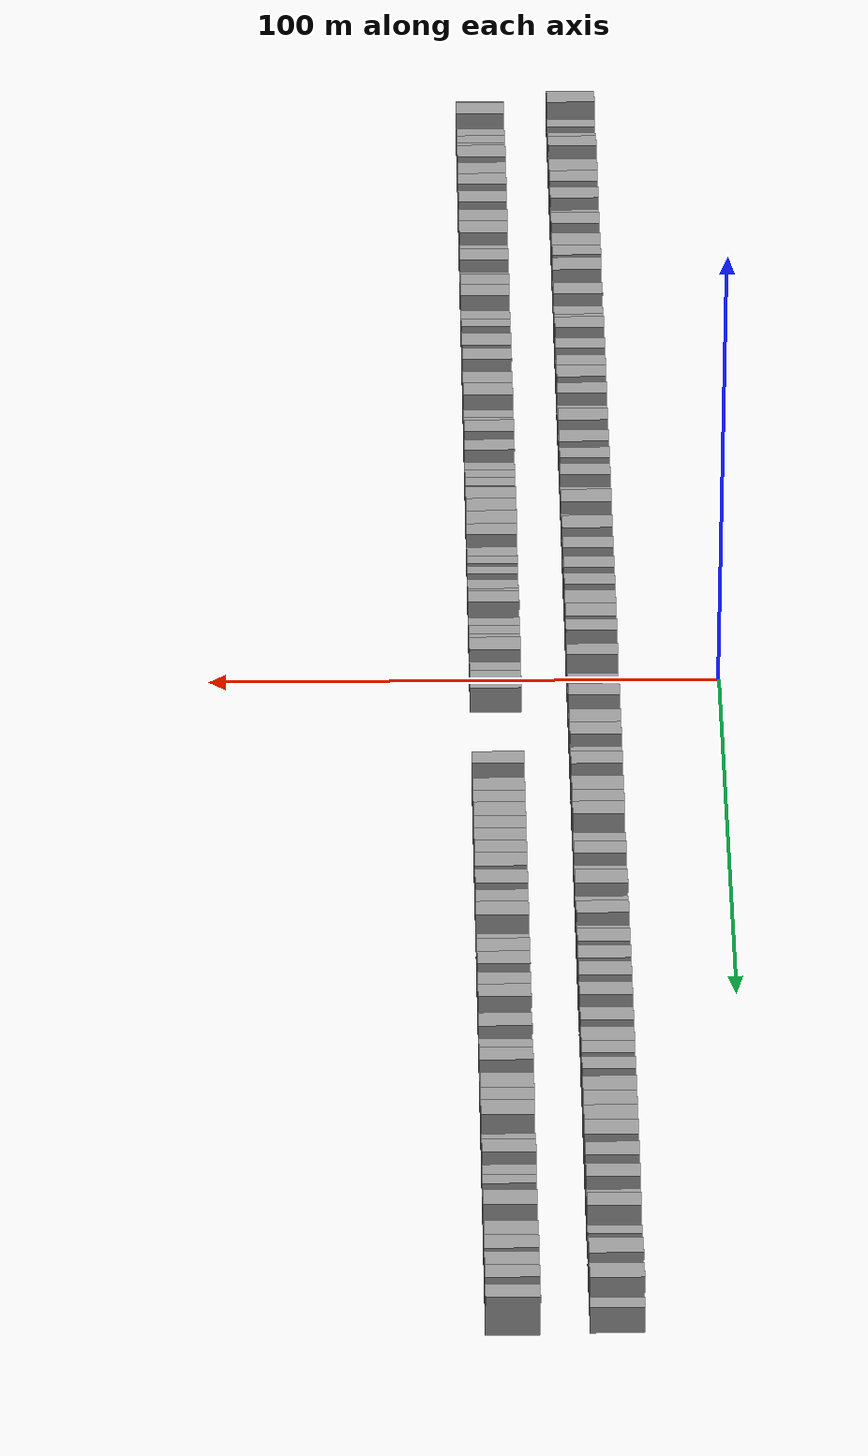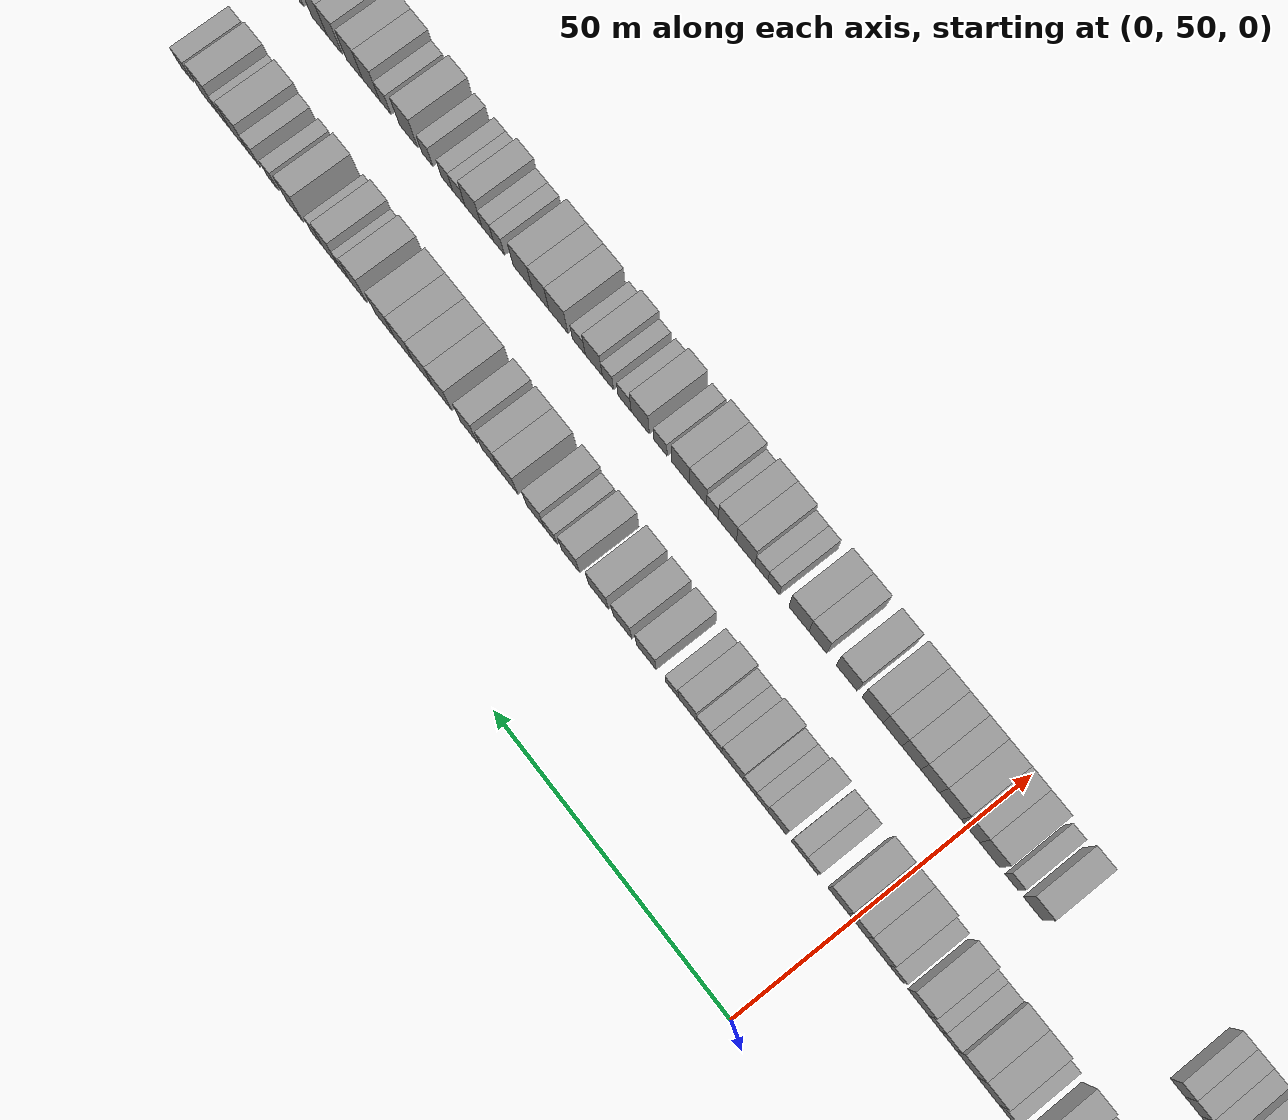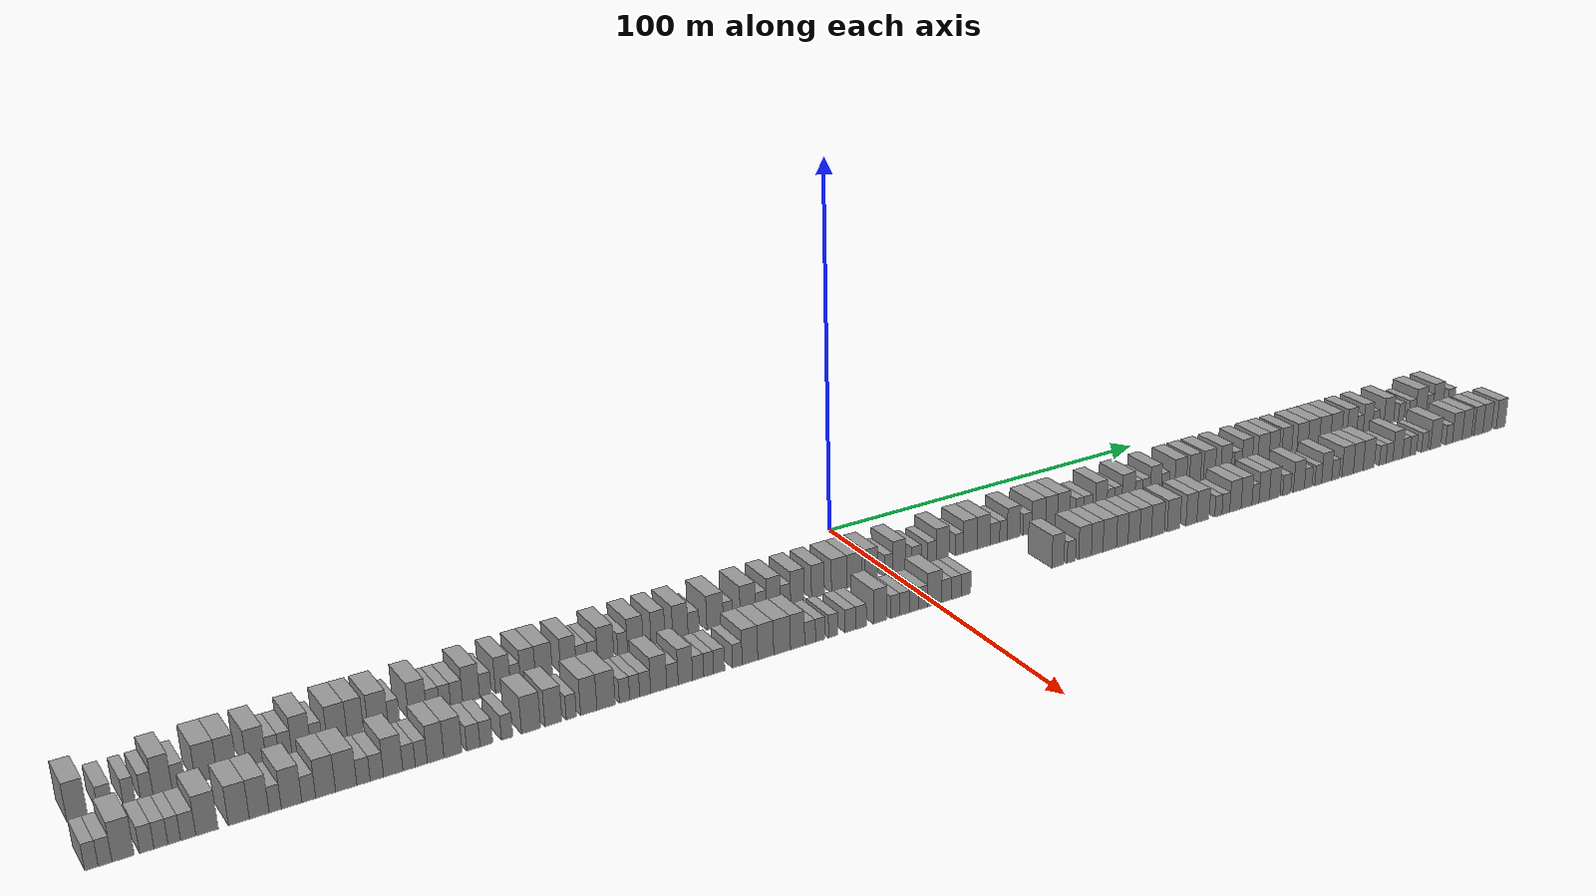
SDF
<sdf version="1.6">
 <world name="default">
  <scene>
   <sky><clouds><speed>12</speed></clouds></sky>
   <ambient>0.4 0.4 0.4 1</ambient>
   <background>0.7 0.7 0.7 1</background>
   <shadows>1</shadows>
  </scene>
  <gravity>0 0 -9.8066</gravity>
  <magnetic_field>6e-06 2.3e-05 -4.2e-05</magnetic_field>
  <physics default="0" name="default_physics" type="ode">
   <ode>
    <solver>
     <type>quick</type>
     <iters>10</iters>
     <sor>1.0</sor>
     <use_dynamic_moi_rescaling>0</use_dynamic_moi_rescaling>
    </solver>
    <constraints>
     <cfm>0</cfm>
     <erp>0.2</erp>
     <contact_max_correcting_vel>100</contact_max_correcting_vel>
     <contact_surface_layer>0.001</contact_surface_layer>
    </constraints>
   </ode>
   <max_step_size>0.004</max_step_size>
   <real_time_factor>1</real_time_factor>
   <real_time_update_rate>250</real_time_update_rate>
  </physics>
  <light name="sun" type="directional">
   <pose>0 0 10 0 0 0</pose>
   <diffuse>0.8 0.8 0.8 1</diffuse>
   <specular>0.2 0.2 0.2 1</specular>
   <attenuation>
    <range>1000</range>
    <constant>0.9</constant>
    <linear>0.01</linear>
    <quadratic>0.001</quadratic>
   </attenuation>
   <direction>-0.5 0.1 -0.9</direction>
  </light>
  <model name="building_1">
   <static>1</static>
   <pose>25.0000 -194.9963 0 0.000000 0.000000 0.000000</pose>
   <link name="link">
    <pose>0 0 4.50 0 0 0</pose>
    <collision name="collision"><geometry><box><size>10.0000 4.0073 9.0000</size></box></geometry></collision>
    <visual name="visual">
     <cast_shadows>0</cast_shadows>
     <geometry><box><size>10.0000 4.0073 9.0000</size></box></geometry>
     <material>
      <script>
       <uri>model://grey_wall/materials/scripts</uri>
       <uri>model://grey_wall/materials/textures</uri>
       <name>vrc/grey_wall</name>
      </script>
     </material>
    </visual>
   </link>
  </model>
  <model name="building_2">
   <static>1</static>
   <pose>25.0000 -189.5144 0 0.000000 0.000000 0.000000</pose>
   <link name="link">
    <pose>0 0 3.00 0 0 0</pose>
    <collision name="collision"><geometry><box><size>10.0000 2.9565 6.0000</size></box></geometry></collision>
    <visual name="visual">
     <cast_shadows>0</cast_shadows>
     <geometry><box><size>10.0000 2.9565 6.0000</size></box></geometry>
     <material>
      <script>
       <uri>model://grey_wall/materials/scripts</uri>
       <uri>model://grey_wall/materials/textures</uri>
       <name>vrc/grey_wall</name>
      </script>
     </material>
    </visual>
   </link>
  </model>
  <model name="building_3">
   <static>1</static>
   <pose>25.0000 -184.8351 0 0.000000 0.000000 0.000000</pose>
   <link name="link">
    <pose>0 0 3.00 0 0 0</pose>
    <collision name="collision"><geometry><box><size>10.0000 2.4023 6.0000</size></box></geometry></collision>
    <visual name="visual">
     <cast_shadows>0</cast_shadows>
     <geometry><box><size>10.0000 2.4023 6.0000</size></box></geometry>
     <material>
      <script>
       <uri>model://grey_wall/materials/scripts</uri>
       <uri>model://grey_wall/materials/textures</uri>
       <name>vrc/grey_wall</name>
      </script>
     </material>
    </visual>
   </link>
  </model>
  <model name="building_4">
   <static>1</static>
   <pose>25.0000 -181.3856 0 0.000000 0.000000 0.000000</pose>
   <link name="link">
    <pose>0 0 3.00 0 0 0</pose>
    <collision name="collision"><geometry><box><size>10.0000 2.4968 6.0000</size></box></geometry></collision>
    <visual name="visual">
     <cast_shadows>0</cast_shadows>
     <geometry><box><size>10.0000 2.4968 6.0000</size></box></geometry>
     <material>
      <script>
       <uri>model://grey_wall/materials/scripts</uri>
       <uri>model://grey_wall/materials/textures</uri>
       <name>vrc/grey_wall</name>
      </script>
     </material>
    </visual>
   </link>
  </model>
  <model name="building_5">
   <static>1</static>
   <pose>25.0000 -178.2286 0 0.000000 0.000000 0.000000</pose>
   <link name="link">
    <pose>0 0 4.50 0 0 0</pose>
    <collision name="collision"><geometry><box><size>10.0000 3.8172 9.0000</size></box></geometry></collision>
    <visual name="visual">
     <cast_shadows>0</cast_shadows>
     <geometry><box><size>10.0000 3.8172 9.0000</size></box></geometry>
     <material>
      <script>
       <uri>model://grey_wall/materials/scripts</uri>
       <uri>model://grey_wall/materials/textures</uri>
       <name>vrc/grey_wall</name>
      </script>
     </material>
    </visual>
   </link>
  </model>
  <model name="building_6">
   <static>1</static>
   <pose>25.0000 -174.9447 0 0.000000 0.000000 0.000000</pose>
   <link name="link">
    <pose>0 0 3.00 0 0 0</pose>
    <collision name="collision"><geometry><box><size>10.0000 2.7505 6.0000</size></box></geometry></collision>
    <visual name="visual">
     <cast_shadows>0</cast_shadows>
     <geometry><box><size>10.0000 2.7505 6.0000</size></box></geometry>
     <material>
      <script>
       <uri>model://grey_wall/materials/scripts</uri>
       <uri>model://grey_wall/materials/textures</uri>
       <name>vrc/grey_wall</name>
      </script>
     </material>
    </visual>
   </link>
  </model>
  <model name="building_7">
   <static>1</static>
   <pose>25.0000 -169.3398 0 0.000000 0.000000 0.000000</pose>
   <link name="link">
    <pose>0 0 4.50 0 0 0</pose>
    <collision name="collision"><geometry><box><size>10.0000 4.4594 9.0000</size></box></geometry></collision>
    <visual name="visual">
     <cast_shadows>0</cast_shadows>
     <geometry><box><size>10.0000 4.4594 9.0000</size></box></geometry>
     <material>
      <script>
       <uri>model://grey_wall/materials/scripts</uri>
       <uri>model://grey_wall/materials/textures</uri>
       <name>vrc/grey_wall</name>
      </script>
     </material>
    </visual>
   </link>
  </model>
  <model name="building_8">
   <static>1</static>
   <pose>25.0000 -165.0599 0 0.000000 0.000000 0.000000</pose>
   <link name="link">
    <pose>0 0 4.50 0 0 0</pose>
    <collision name="collision"><geometry><box><size>10.0000 4.1004 9.0000</size></box></geometry></collision>
    <visual name="visual">
     <cast_shadows>0</cast_shadows>
     <geometry><box><size>10.0000 4.1004 9.0000</size></box></geometry>
     <material>
      <script>
       <uri>model://grey_wall/materials/scripts</uri>
       <uri>model://grey_wall/materials/textures</uri>
       <name>vrc/grey_wall</name>
      </script>
     </material>
    </visual>
   </link>
  </model>
  <model name="building_9">
   <static>1</static>
   <pose>25.0000 -158.9554 0 0.000000 0.000000 0.000000</pose>
   <link name="link">
    <pose>0 0 4.50 0 0 0</pose>
    <collision name="collision"><geometry><box><size>10.0000 4.1084 9.0000</size></box></geometry></collision>
    <visual name="visual">
     <cast_shadows>0</cast_shadows>
     <geometry><box><size>10.0000 4.1084 9.0000</size></box></geometry>
     <material>
      <script>
       <uri>model://grey_wall/materials/scripts</uri>
       <uri>model://grey_wall/materials/textures</uri>
       <name>vrc/grey_wall</name>
      </script>
     </material>
    </visual>
   </link>
  </model>
  <model name="building_10">
   <static>1</static>
   <pose>25.0000 -155.5419 0 0.000000 0.000000 0.000000</pose>
   <link name="link">
    <pose>0 0 3.00 0 0 0</pose>
    <collision name="collision"><geometry><box><size>10.0000 2.7187 6.0000</size></box></geometry></collision>
    <visual name="visual">
     <cast_shadows>0</cast_shadows>
     <geometry><box><size>10.0000 2.7187 6.0000</size></box></geometry>
     <material>
      <script>
       <uri>model://grey_wall/materials/scripts</uri>
       <uri>model://grey_wall/materials/textures</uri>
       <name>vrc/grey_wall</name>
      </script>
     </material>
    </visual>
   </link>
  </model>
  <model name="building_11">
   <static>1</static>
   <pose>25.0000 -152.8195 0 0.000000 0.000000 0.000000</pose>
   <link name="link">
    <pose>0 0 3.00 0 0 0</pose>
    <collision name="collision"><geometry><box><size>10.0000 2.7261 6.0000</size></box></geometry></collision>
    <visual name="visual">
     <cast_shadows>0</cast_shadows>
     <geometry><box><size>10.0000 2.7261 6.0000</size></box></geometry>
     <material>
      <script>
       <uri>model://grey_wall/materials/scripts</uri>
       <uri>model://grey_wall/materials/textures</uri>
       <name>vrc/grey_wall</name>
      </script>
     </material>
    </visual>
   </link>
  </model>
  <model name="building_12">
   <static>1</static>
   <pose>25.0000 -149.4233 0 0.000000 0.000000 0.000000</pose>
   <link name="link">
    <pose>0 0 4.50 0 0 0</pose>
    <collision name="collision"><geometry><box><size>10.0000 4.0665 9.0000</size></box></geometry></collision>
    <visual name="visual">
     <cast_shadows>0</cast_shadows>
     <geometry><box><size>10.0000 4.0665 9.0000</size></box></geometry>
     <material>
      <script>
       <uri>model://grey_wall/materials/scripts</uri>
       <uri>model://grey_wall/materials/textures</uri>
       <name>vrc/grey_wall</name>
      </script>
     </material>
    </visual>
   </link>
  </model>
  <model name="building_13">
   <static>1</static>
   <pose>25.0000 -146.1263 0 0.000000 0.000000 0.000000</pose>
   <link name="link">
    <pose>0 0 3.00 0 0 0</pose>
    <collision name="collision"><geometry><box><size>10.0000 2.5274 6.0000</size></box></geometry></collision>
    <visual name="visual">
     <cast_shadows>0</cast_shadows>
     <geometry><box><size>10.0000 2.5274 6.0000</size></box></geometry>
     <material>
      <script>
       <uri>model://grey_wall/materials/scripts</uri>
       <uri>model://grey_wall/materials/textures</uri>
       <name>vrc/grey_wall</name>
      </script>
     </material>
    </visual>
   </link>
  </model>
  <model name="building_14">
   <static>1</static>
   <pose>25.0000 -141.6784 0 0.000000 0.000000 0.000000</pose>
   <link name="link">
    <pose>0 0 4.50 0 0 0</pose>
    <collision name="collision"><geometry><box><size>10.0000 4.3684 9.0000</size></box></geometry></collision>
    <visual name="visual">
     <cast_shadows>0</cast_shadows>
     <geometry><box><size>10.0000 4.3684 9.0000</size></box></geometry>
     <material>
      <script>
       <uri>model://grey_wall/materials/scripts</uri>
       <uri>model://grey_wall/materials/textures</uri>
       <name>vrc/grey_wall</name>
      </script>
     </material>
    </visual>
   </link>
  </model>
  <model name="building_15">
   <static>1</static>
   <pose>25.0000 -137.6633 0 0.000000 0.000000 0.000000</pose>
   <link name="link">
    <pose>0 0 4.50 0 0 0</pose>
    <collision name="collision"><geometry><box><size>10.0000 3.6618 9.0000</size></box></geometry></collision>
    <visual name="visual">
     <cast_shadows>0</cast_shadows>
     <geometry><box><size>10.0000 3.6618 9.0000</size></box></geometry>
     <material>
      <script>
       <uri>model://grey_wall/materials/scripts</uri>
       <uri>model://grey_wall/materials/textures</uri>
       <name>vrc/grey_wall</name>
      </script>
     </material>
    </visual>
   </link>
  </model>
  <model name="building_16">
   <static>1</static>
   <pose>25.0000 -132.6018 0 0.000000 0.000000 0.000000</pose>
   <link name="link">
    <pose>0 0 4.50 0 0 0</pose>
    <collision name="collision"><geometry><box><size>10.0000 4.4613 9.0000</size></box></geometry></collision>
    <visual name="visual">
     <cast_shadows>0</cast_shadows>
     <geometry><box><size>10.0000 4.4613 9.0000</size></box></geometry>
     <material>
      <script>
       <uri>model://grey_wall/materials/scripts</uri>
       <uri>model://grey_wall/materials/textures</uri>
       <name>vrc/grey_wall</name>
      </script>
     </material>
    </visual>
   </link>
  </model>
  <model name="building_17">
   <static>1</static>
   <pose>25.0000 -129.0669 0 0.000000 0.000000 0.000000</pose>
   <link name="link">
    <pose>0 0 3.00 0 0 0</pose>
    <collision name="collision"><geometry><box><size>10.0000 2.6084 6.0000</size></box></geometry></collision>
    <visual name="visual">
     <cast_shadows>0</cast_shadows>
     <geometry><box><size>10.0000 2.6084 6.0000</size></box></geometry>
     <material>
      <script>
       <uri>model://grey_wall/materials/scripts</uri>
       <uri>model://grey_wall/materials/textures</uri>
       <name>vrc/grey_wall</name>
      </script>
     </material>
    </visual>
   </link>
  </model>
  <model name="building_18">
   <static>1</static>
   <pose>25.0000 -123.7205 0 0.000000 0.000000 0.000000</pose>
   <link name="link">
    <pose>0 0 4.50 0 0 0</pose>
    <collision name="collision"><geometry><box><size>10.0000 4.0843 9.0000</size></box></geometry></collision>
    <visual name="visual">
     <cast_shadows>0</cast_shadows>
     <geometry><box><size>10.0000 4.0843 9.0000</size></box></geometry>
     <material>
      <script>
       <uri>model://grey_wall/materials/scripts</uri>
       <uri>model://grey_wall/materials/textures</uri>
       <name>vrc/grey_wall</name>
      </script>
     </material>
    </visual>
   </link>
  </model>
  <model name="building_19">
   <static>1</static>
   <pose>25.0000 -120.1962 0 0.000000 0.000000 0.000000</pose>
   <link name="link">
    <pose>0 0 3.00 0 0 0</pose>
    <collision name="collision"><geometry><box><size>10.0000 2.9643 6.0000</size></box></geometry></collision>
    <visual name="visual">
     <cast_shadows>0</cast_shadows>
     <geometry><box><size>10.0000 2.9643 6.0000</size></box></geometry>
     <material>
      <script>
       <uri>model://grey_wall/materials/scripts</uri>
       <uri>model://grey_wall/materials/textures</uri>
       <name>vrc/grey_wall</name>
      </script>
     </material>
    </visual>
   </link>
  </model>
  <model name="building_20">
   <static>1</static>
   <pose>25.0000 -117.4241 0 0.000000 0.000000 0.000000</pose>
   <link name="link">
    <pose>0 0 3.00 0 0 0</pose>
    <collision name="collision"><geometry><box><size>10.0000 2.5798 6.0000</size></box></geometry></collision>
    <visual name="visual">
     <cast_shadows>0</cast_shadows>
     <geometry><box><size>10.0000 2.5798 6.0000</size></box></geometry>
     <material>
      <script>
       <uri>model://grey_wall/materials/scripts</uri>
       <uri>model://grey_wall/materials/textures</uri>
       <name>vrc/grey_wall</name>
      </script>
     </material>
    </visual>
   </link>
  </model>
  <model name="building_21">
   <static>1</static>
   <pose>25.0000 -114.7370 0 0.000000 0.000000 0.000000</pose>
   <link name="link">
    <pose>0 0 3.00 0 0 0</pose>
    <collision name="collision"><geometry><box><size>10.0000 2.7944 6.0000</size></box></geometry></collision>
    <visual name="visual">
     <cast_shadows>0</cast_shadows>
     <geometry><box><size>10.0000 2.7944 6.0000</size></box></geometry>
     <material>
      <script>
       <uri>model://grey_wall/materials/scripts</uri>
       <uri>model://grey_wall/materials/textures</uri>
       <name>vrc/grey_wall</name>
      </script>
     </material>
    </visual>
   </link>
  </model>
  <model name="building_22">
   <static>1</static>
   <pose>25.0000 -111.3566 0 0.000000 0.000000 0.000000</pose>
   <link name="link">
    <pose>0 0 4.50 0 0 0</pose>
    <collision name="collision"><geometry><box><size>10.0000 3.9664 9.0000</size></box></geometry></collision>
    <visual name="visual">
     <cast_shadows>0</cast_shadows>
     <geometry><box><size>10.0000 3.9664 9.0000</size></box></geometry>
     <material>
      <script>
       <uri>model://grey_wall/materials/scripts</uri>
       <uri>model://grey_wall/materials/textures</uri>
       <name>vrc/grey_wall</name>
      </script>
     </material>
    </visual>
   </link>
  </model>
  <model name="building_23">
   <static>1</static>
   <pose>25.0000 -107.9977 0 0.000000 0.000000 0.000000</pose>
   <link name="link">
    <pose>0 0 3.00 0 0 0</pose>
    <collision name="collision"><geometry><box><size>10.0000 2.7516 6.0000</size></box></geometry></collision>
    <visual name="visual">
     <cast_shadows>0</cast_shadows>
     <geometry><box><size>10.0000 2.7516 6.0000</size></box></geometry>
     <material>
      <script>
       <uri>model://grey_wall/materials/scripts</uri>
       <uri>model://grey_wall/materials/textures</uri>
       <name>vrc/grey_wall</name>
      </script>
     </material>
    </visual>
   </link>
  </model>
  <model name="building_24">
   <static>1</static>
   <pose>25.0000 -103.8148 0 0.000000 0.000000 0.000000</pose>
   <link name="link">
    <pose>0 0 4.50 0 0 0</pose>
    <collision name="collision"><geometry><box><size>10.0000 3.6142 9.0000</size></box></geometry></collision>
    <visual name="visual">
     <cast_shadows>0</cast_shadows>
     <geometry><box><size>10.0000 3.6142 9.0000</size></box></geometry>
     <material>
      <script>
       <uri>model://grey_wall/materials/scripts</uri>
       <uri>model://grey_wall/materials/textures</uri>
       <name>vrc/grey_wall</name>
      </script>
     </material>
    </visual>
   </link>
  </model>
  <model name="building_25">
   <static>1</static>
   <pose>25.0000 -100.7934 0 0.000000 0.000000 0.000000</pose>
   <link name="link">
    <pose>0 0 3.00 0 0 0</pose>
    <collision name="collision"><geometry><box><size>10.0000 2.4286 6.0000</size></box></geometry></collision>
    <visual name="visual">
     <cast_shadows>0</cast_shadows>
     <geometry><box><size>10.0000 2.4286 6.0000</size></box></geometry>
     <material>
      <script>
       <uri>model://grey_wall/materials/scripts</uri>
       <uri>model://grey_wall/materials/textures</uri>
       <name>vrc/grey_wall</name>
      </script>
     </material>
    </visual>
   </link>
  </model>
  <model name="building_26">
   <static>1</static>
   <pose>25.0000 -97.7756 0 0.000000 0.000000 0.000000</pose>
   <link name="link">
    <pose>0 0 4.50 0 0 0</pose>
    <collision name="collision"><geometry><box><size>10.0000 3.6071 9.0000</size></box></geometry></collision>
    <visual name="visual">
     <cast_shadows>0</cast_shadows>
     <geometry><box><size>10.0000 3.6071 9.0000</size></box></geometry>
     <material>
      <script>
       <uri>model://grey_wall/materials/scripts</uri>
       <uri>model://grey_wall/materials/textures</uri>
       <name>vrc/grey_wall</name>
      </script>
     </material>
    </visual>
   </link>
  </model>
  <model name="building_27">
   <static>1</static>
   <pose>25.0000 -93.9097 0 0.000000 0.000000 0.000000</pose>
   <link name="link">
    <pose>0 0 4.50 0 0 0</pose>
    <collision name="collision"><geometry><box><size>10.0000 4.1248 9.0000</size></box></geometry></collision>
    <visual name="visual">
     <cast_shadows>0</cast_shadows>
     <geometry><box><size>10.0000 4.1248 9.0000</size></box></geometry>
     <material>
      <script>
       <uri>model://grey_wall/materials/scripts</uri>
       <uri>model://grey_wall/materials/textures</uri>
       <name>vrc/grey_wall</name>
      </script>
     </material>
    </visual>
   </link>
  </model>
  <model name="building_28">
   <static>1</static>
   <pose>25.0000 -87.9242 0 0.000000 0.000000 0.000000</pose>
   <link name="link">
    <pose>0 0 4.50 0 0 0</pose>
    <collision name="collision"><geometry><box><size>10.0000 3.8462 9.0000</size></box></geometry></collision>
    <visual name="visual">
     <cast_shadows>0</cast_shadows>
     <geometry><box><size>10.0000 3.8462 9.0000</size></box></geometry>
     <material>
      <script>
       <uri>model://grey_wall/materials/scripts</uri>
       <uri>model://grey_wall/materials/textures</uri>
       <name>vrc/grey_wall</name>
      </script>
     </material>
    </visual>
   </link>
  </model>
  <model name="building_29">
   <static>1</static>
   <pose>25.0000 -84.5672 0 0.000000 0.000000 0.000000</pose>
   <link name="link">
    <pose>0 0 3.00 0 0 0</pose>
    <collision name="collision"><geometry><box><size>10.0000 2.8677 6.0000</size></box></geometry></collision>
    <visual name="visual">
     <cast_shadows>0</cast_shadows>
     <geometry><box><size>10.0000 2.8677 6.0000</size></box></geometry>
     <material>
      <script>
       <uri>model://grey_wall/materials/scripts</uri>
       <uri>model://grey_wall/materials/textures</uri>
       <name>vrc/grey_wall</name>
      </script>
     </material>
    </visual>
   </link>
  </model>
  <model name="building_30">
   <static>1</static>
   <pose>25.0000 -81.9116 0 0.000000 0.000000 0.000000</pose>
   <link name="link">
    <pose>0 0 3.00 0 0 0</pose>
    <collision name="collision"><geometry><box><size>10.0000 2.4435 6.0000</size></box></geometry></collision>
    <visual name="visual">
     <cast_shadows>0</cast_shadows>
     <geometry><box><size>10.0000 2.4435 6.0000</size></box></geometry>
     <material>
      <script>
       <uri>model://grey_wall/materials/scripts</uri>
       <uri>model://grey_wall/materials/textures</uri>
       <name>vrc/grey_wall</name>
      </script>
     </material>
    </visual>
   </link>
  </model>
  <model name="building_31">
   <static>1</static>
   <pose>25.0000 -78.6336 0 0.000000 0.000000 0.000000</pose>
   <link name="link">
    <pose>0 0 4.50 0 0 0</pose>
    <collision name="collision"><geometry><box><size>10.0000 4.1126 9.0000</size></box></geometry></collision>
    <visual name="visual">
     <cast_shadows>0</cast_shadows>
     <geometry><box><size>10.0000 4.1126 9.0000</size></box></geometry>
     <material>
      <script>
       <uri>model://grey_wall/materials/scripts</uri>
       <uri>model://grey_wall/materials/textures</uri>
       <name>vrc/grey_wall</name>
      </script>
     </material>
    </visual>
   </link>
  </model>
  <model name="building_32">
   <static>1</static>
   <pose>25.0000 -74.3386 0 0.000000 0.000000 0.000000</pose>
   <link name="link">
    <pose>0 0 3.00 0 0 0</pose>
    <collision name="collision"><geometry><box><size>10.0000 2.4773 6.0000</size></box></geometry></collision>
    <visual name="visual">
     <cast_shadows>0</cast_shadows>
     <geometry><box><size>10.0000 2.4773 6.0000</size></box></geometry>
     <material>
      <script>
       <uri>model://grey_wall/materials/scripts</uri>
       <uri>model://grey_wall/materials/textures</uri>
       <name>vrc/grey_wall</name>
      </script>
     </material>
    </visual>
   </link>
  </model>
  <model name="building_33">
   <static>1</static>
   <pose>25.0000 -71.0812 0 0.000000 0.000000 0.000000</pose>
   <link name="link">
    <pose>0 0 4.50 0 0 0</pose>
    <collision name="collision"><geometry><box><size>10.0000 4.0374 9.0000</size></box></geometry></collision>
    <visual name="visual">
     <cast_shadows>0</cast_shadows>
     <geometry><box><size>10.0000 4.0374 9.0000</size></box></geometry>
     <material>
      <script>
       <uri>model://grey_wall/materials/scripts</uri>
       <uri>model://grey_wall/materials/textures</uri>
       <name>vrc/grey_wall</name>
      </script>
     </material>
    </visual>
   </link>
  </model>
  <model name="building_34">
   <static>1</static>
   <pose>25.0000 -65.2524 0 0.000000 0.000000 0.000000</pose>
   <link name="link">
    <pose>0 0 4.50 0 0 0</pose>
    <collision name="collision"><geometry><box><size>10.0000 3.6204 9.0000</size></box></geometry></collision>
    <visual name="visual">
     <cast_shadows>0</cast_shadows>
     <geometry><box><size>10.0000 3.6204 9.0000</size></box></geometry>
     <material>
      <script>
       <uri>model://grey_wall/materials/scripts</uri>
       <uri>model://grey_wall/materials/textures</uri>
       <name>vrc/grey_wall</name>
      </script>
     </material>
    </visual>
   </link>
  </model>
  <model name="building_35">
   <static>1</static>
   <pose>25.0000 -59.4481 0 0.000000 0.000000 0.000000</pose>
   <link name="link">
    <pose>0 0 4.50 0 0 0</pose>
    <collision name="collision"><geometry><box><size>10.0000 3.9881 9.0000</size></box></geometry></collision>
    <visual name="visual">
     <cast_shadows>0</cast_shadows>
     <geometry><box><size>10.0000 3.9881 9.0000</size></box></geometry>
     <material>
      <script>
       <uri>model://grey_wall/materials/scripts</uri>
       <uri>model://grey_wall/materials/textures</uri>
       <name>vrc/grey_wall</name>
      </script>
     </material>
    </visual>
   </link>
  </model>
  <model name="building_36">
   <static>1</static>
   <pose>25.0000 -55.9549 0 0.000000 0.000000 0.000000</pose>
   <link name="link">
    <pose>0 0 3.00 0 0 0</pose>
    <collision name="collision"><geometry><box><size>10.0000 2.9984 6.0000</size></box></geometry></collision>
    <visual name="visual">
     <cast_shadows>0</cast_shadows>
     <geometry><box><size>10.0000 2.9984 6.0000</size></box></geometry>
     <material>
      <script>
       <uri>model://grey_wall/materials/scripts</uri>
       <uri>model://grey_wall/materials/textures</uri>
       <name>vrc/grey_wall</name>
      </script>
     </material>
    </visual>
   </link>
  </model>
  <model name="building_37">
   <static>1</static>
   <pose>25.0000 -50.2555 0 0.000000 0.000000 0.000000</pose>
   <link name="link">
    <pose>0 0 4.50 0 0 0</pose>
    <collision name="collision"><geometry><box><size>10.0000 4.4004 9.0000</size></box></geometry></collision>
    <visual name="visual">
     <cast_shadows>0</cast_shadows>
     <geometry><box><size>10.0000 4.4004 9.0000</size></box></geometry>
     <material>
      <script>
       <uri>model://grey_wall/materials/scripts</uri>
       <uri>model://grey_wall/materials/textures</uri>
       <name>vrc/grey_wall</name>
      </script>
     </material>
    </visual>
   </link>
  </model>
  <model name="building_38">
   <static>1</static>
   <pose>25.0000 -46.7610 0 0.000000 0.000000 0.000000</pose>
   <link name="link">
    <pose>0 0 3.00 0 0 0</pose>
    <collision name="collision"><geometry><box><size>10.0000 2.5888 6.0000</size></box></geometry></collision>
    <visual name="visual">
     <cast_shadows>0</cast_shadows>
     <geometry><box><size>10.0000 2.5888 6.0000</size></box></geometry>
     <material>
      <script>
       <uri>model://grey_wall/materials/scripts</uri>
       <uri>model://grey_wall/materials/textures</uri>
       <name>vrc/grey_wall</name>
      </script>
     </material>
    </visual>
   </link>
  </model>
  <model name="building_39">
   <static>1</static>
   <pose>25.0000 -41.3488 0 0.000000 0.000000 0.000000</pose>
   <link name="link">
    <pose>0 0 4.50 0 0 0</pose>
    <collision name="collision"><geometry><box><size>10.0000 4.2356 9.0000</size></box></geometry></collision>
    <visual name="visual">
     <cast_shadows>0</cast_shadows>
     <geometry><box><size>10.0000 4.2356 9.0000</size></box></geometry>
     <material>
      <script>
       <uri>model://grey_wall/materials/scripts</uri>
       <uri>model://grey_wall/materials/textures</uri>
       <name>vrc/grey_wall</name>
      </script>
     </material>
    </visual>
   </link>
  </model>
  <model name="building_40">
   <static>1</static>
   <pose>25.0000 -37.7375 0 0.000000 0.000000 0.000000</pose>
   <link name="link">
    <pose>0 0 3.00 0 0 0</pose>
    <collision name="collision"><geometry><box><size>10.0000 2.9869 6.0000</size></box></geometry></collision>
    <visual name="visual">
     <cast_shadows>0</cast_shadows>
     <geometry><box><size>10.0000 2.9869 6.0000</size></box></geometry>
     <material>
      <script>
       <uri>model://grey_wall/materials/scripts</uri>
       <uri>model://grey_wall/materials/textures</uri>
       <name>vrc/grey_wall</name>
      </script>
     </material>
    </visual>
   </link>
  </model>
  <model name="building_41">
   <static>1</static>
   <pose>25.0000 -34.2889 0 0.000000 0.000000 0.000000</pose>
   <link name="link">
    <pose>0 0 4.50 0 0 0</pose>
    <collision name="collision"><geometry><box><size>10.0000 3.9105 9.0000</size></box></geometry></collision>
    <visual name="visual">
     <cast_shadows>0</cast_shadows>
     <geometry><box><size>10.0000 3.9105 9.0000</size></box></geometry>
     <material>
      <script>
       <uri>model://grey_wall/materials/scripts</uri>
       <uri>model://grey_wall/materials/textures</uri>
       <name>vrc/grey_wall</name>
      </script>
     </material>
    </visual>
   </link>
  </model>
  <model name="building_42">
   <static>1</static>
   <pose>25.0000 -30.9628 0 0.000000 0.000000 0.000000</pose>
   <link name="link">
    <pose>0 0 3.00 0 0 0</pose>
    <collision name="collision"><geometry><box><size>10.0000 2.7416 6.0000</size></box></geometry></collision>
    <visual name="visual">
     <cast_shadows>0</cast_shadows>
     <geometry><box><size>10.0000 2.7416 6.0000</size></box></geometry>
     <material>
      <script>
       <uri>model://grey_wall/materials/scripts</uri>
       <uri>model://grey_wall/materials/textures</uri>
       <name>vrc/grey_wall</name>
      </script>
     </material>
    </visual>
   </link>
  </model>
  <model name="building_43">
   <static>1</static>
   <pose>25.0000 -27.6589 0 0.000000 0.000000 0.000000</pose>
   <link name="link">
    <pose>0 0 4.50 0 0 0</pose>
    <collision name="collision"><geometry><box><size>10.0000 3.8662 9.0000</size></box></geometry></collision>
    <visual name="visual">
     <cast_shadows>0</cast_shadows>
     <geometry><box><size>10.0000 3.8662 9.0000</size></box></geometry>
     <material>
      <script>
       <uri>model://grey_wall/materials/scripts</uri>
       <uri>model://grey_wall/materials/textures</uri>
       <name>vrc/grey_wall</name>
      </script>
     </material>
    </visual>
   </link>
  </model>
  <model name="building_44">
   <static>1</static>
   <pose>25.0000 -21.8869 0 0.000000 0.000000 0.000000</pose>
   <link name="link">
    <pose>0 0 4.50 0 0 0</pose>
    <collision name="collision"><geometry><box><size>10.0000 3.6778 9.0000</size></box></geometry></collision>
    <visual name="visual">
     <cast_shadows>0</cast_shadows>
     <geometry><box><size>10.0000 3.6778 9.0000</size></box></geometry>
     <material>
      <script>
       <uri>model://grey_wall/materials/scripts</uri>
       <uri>model://grey_wall/materials/textures</uri>
       <name>vrc/grey_wall</name>
      </script>
     </material>
    </visual>
   </link>
  </model>
  <model name="building_45">
   <static>1</static>
   <pose>25.0000 -15.8329 0 0.000000 0.000000 0.000000</pose>
   <link name="link">
    <pose>0 0 4.50 0 0 0</pose>
    <collision name="collision"><geometry><box><size>10.0000 4.4302 9.0000</size></box></geometry></collision>
    <visual name="visual">
     <cast_shadows>0</cast_shadows>
     <geometry><box><size>10.0000 4.4302 9.0000</size></box></geometry>
     <material>
      <script>
       <uri>model://grey_wall/materials/scripts</uri>
       <uri>model://grey_wall/materials/textures</uri>
       <name>vrc/grey_wall</name>
      </script>
     </material>
    </visual>
   </link>
  </model>
  <model name="building_46">
   <static>1</static>
   <pose>25.0000 -11.4531 0 0.000000 0.000000 0.000000</pose>
   <link name="link">
    <pose>0 0 4.50 0 0 0</pose>
    <collision name="collision"><geometry><box><size>10.0000 4.3293 9.0000</size></box></geometry></collision>
    <visual name="visual">
     <cast_shadows>0</cast_shadows>
     <geometry><box><size>10.0000 4.3293 9.0000</size></box></geometry>
     <material>
      <script>
       <uri>model://grey_wall/materials/scripts</uri>
       <uri>model://grey_wall/materials/textures</uri>
       <name>vrc/grey_wall</name>
      </script>
     </material>
    </visual>
   </link>
  </model>
  <model name="building_47">
   <static>1</static>
   <pose>25.0000 -6.4821 0 0.000000 0.000000 0.000000</pose>
   <link name="link">
    <pose>0 0 4.50 0 0 0</pose>
    <collision name="collision"><geometry><box><size>10.0000 3.6127 9.0000</size></box></geometry></collision>
    <visual name="visual">
     <cast_shadows>0</cast_shadows>
     <geometry><box><size>10.0000 3.6127 9.0000</size></box></geometry>
     <material>
      <script>
       <uri>model://grey_wall/materials/scripts</uri>
       <uri>model://grey_wall/materials/textures</uri>
       <name>vrc/grey_wall</name>
      </script>
     </material>
    </visual>
   </link>
  </model>
  <model name="building_48">
   <static>1</static>
   <pose>25.0000 -1.4025 0 0.000000 0.000000 0.000000</pose>
   <link name="link">
    <pose>0 0 3.00 0 0 0</pose>
    <collision name="collision"><geometry><box><size>10.0000 2.5464 6.0000</size></box></geometry></collision>
    <visual name="visual">
     <cast_shadows>0</cast_shadows>
     <geometry><box><size>10.0000 2.5464 6.0000</size></box></geometry>
     <material>
      <script>
       <uri>model://grey_wall/materials/scripts</uri>
       <uri>model://grey_wall/materials/textures</uri>
       <name>vrc/grey_wall</name>
      </script>
     </material>
    </visual>
   </link>
  </model>
  <model name="building_49">
   <static>1</static>
   <pose>25.0000 1.7105 0 0.000000 0.000000 0.000000</pose>
   <link name="link">
    <pose>0 0 4.50 0 0 0</pose>
    <collision name="collision"><geometry><box><size>10.0000 3.6796 9.0000</size></box></geometry></collision>
    <visual name="visual">
     <cast_shadows>0</cast_shadows>
     <geometry><box><size>10.0000 3.6796 9.0000</size></box></geometry>
     <material>
      <script>
       <uri>model://grey_wall/materials/scripts</uri>
       <uri>model://grey_wall/materials/textures</uri>
       <name>vrc/grey_wall</name>
      </script>
     </material>
    </visual>
   </link>
  </model>
  <model name="building_50">
   <static>1</static>
   <pose>25.0000 6.9176 0 0.000000 0.000000 0.000000</pose>
   <link name="link">
    <pose>0 0 3.00 0 0 0</pose>
    <collision name="collision"><geometry><box><size>10.0000 2.7346 6.0000</size></box></geometry></collision>
    <visual name="visual">
     <cast_shadows>0</cast_shadows>
     <geometry><box><size>10.0000 2.7346 6.0000</size></box></geometry>
     <material>
      <script>
       <uri>model://grey_wall/materials/scripts</uri>
       <uri>model://grey_wall/materials/textures</uri>
       <name>vrc/grey_wall</name>
      </script>
     </material>
    </visual>
   </link>
  </model>
  <model name="building_51">
   <static>1</static>
   <pose>25.0000 11.6050 0 0.000000 0.000000 0.000000</pose>
   <link name="link">
    <pose>0 0 3.00 0 0 0</pose>
    <collision name="collision"><geometry><box><size>10.0000 2.6404 6.0000</size></box></geometry></collision>
    <visual name="visual">
     <cast_shadows>0</cast_shadows>
     <geometry><box><size>10.0000 2.6404 6.0000</size></box></geometry>
     <material>
      <script>
       <uri>model://grey_wall/materials/scripts</uri>
       <uri>model://grey_wall/materials/textures</uri>
       <name>vrc/grey_wall</name>
      </script>
     </material>
    </visual>
   </link>
  </model>
  <model name="building_52">
   <static>1</static>
   <pose>25.0000 14.8452 0 0.000000 0.000000 0.000000</pose>
   <link name="link">
    <pose>0 0 4.50 0 0 0</pose>
    <collision name="collision"><geometry><box><size>10.0000 3.8400 9.0000</size></box></geometry></collision>
    <visual name="visual">
     <cast_shadows>0</cast_shadows>
     <geometry><box><size>10.0000 3.8400 9.0000</size></box></geometry>
     <material>
      <script>
       <uri>model://grey_wall/materials/scripts</uri>
       <uri>model://grey_wall/materials/textures</uri>
       <name>vrc/grey_wall</name>
      </script>
     </material>
    </visual>
   </link>
  </model>
  <model name="building_53">
   <static>1</static>
   <pose>25.0000 20.0217 0 0.000000 0.000000 0.000000</pose>
   <link name="link">
    <pose>0 0 3.00 0 0 0</pose>
    <collision name="collision"><geometry><box><size>10.0000 2.5130 6.0000</size></box></geometry></collision>
    <visual name="visual">
     <cast_shadows>0</cast_shadows>
     <geometry><box><size>10.0000 2.5130 6.0000</size></box></geometry>
     <material>
      <script>
       <uri>model://grey_wall/materials/scripts</uri>
       <uri>model://grey_wall/materials/textures</uri>
       <name>vrc/grey_wall</name>
      </script>
     </material>
    </visual>
   </link>
  </model>
  <model name="building_54">
   <static>1</static>
   <pose>25.0000 23.4024 0 0.000000 0.000000 0.000000</pose>
   <link name="link">
    <pose>0 0 4.50 0 0 0</pose>
    <collision name="collision"><geometry><box><size>10.0000 4.2483 9.0000</size></box></geometry></collision>
    <visual name="visual">
     <cast_shadows>0</cast_shadows>
     <geometry><box><size>10.0000 4.2483 9.0000</size></box></geometry>
     <material>
      <script>
       <uri>model://grey_wall/materials/scripts</uri>
       <uri>model://grey_wall/materials/textures</uri>
       <name>vrc/grey_wall</name>
      </script>
     </material>
    </visual>
   </link>
  </model>
  <model name="building_55">
   <static>1</static>
   <pose>25.0000 27.5710 0 0.000000 0.000000 0.000000</pose>
   <link name="link">
    <pose>0 0 4.50 0 0 0</pose>
    <collision name="collision"><geometry><box><size>10.0000 4.0890 9.0000</size></box></geometry></collision>
    <visual name="visual">
     <cast_shadows>0</cast_shadows>
     <geometry><box><size>10.0000 4.0890 9.0000</size></box></geometry>
     <material>
      <script>
       <uri>model://grey_wall/materials/scripts</uri>
       <uri>model://grey_wall/materials/textures</uri>
       <name>vrc/grey_wall</name>
      </script>
     </material>
    </visual>
   </link>
  </model>
  <model name="building_56">
   <static>1</static>
   <pose>25.0000 31.0874 0 0.000000 0.000000 0.000000</pose>
   <link name="link">
    <pose>0 0 3.00 0 0 0</pose>
    <collision name="collision"><geometry><box><size>10.0000 2.9438 6.0000</size></box></geometry></collision>
    <visual name="visual">
     <cast_shadows>0</cast_shadows>
     <geometry><box><size>10.0000 2.9438 6.0000</size></box></geometry>
     <material>
      <script>
       <uri>model://grey_wall/materials/scripts</uri>
       <uri>model://grey_wall/materials/textures</uri>
       <name>vrc/grey_wall</name>
      </script>
     </material>
    </visual>
   </link>
  </model>
  <model name="building_57">
   <static>1</static>
   <pose>25.0000 33.7737 0 0.000000 0.000000 0.000000</pose>
   <link name="link">
    <pose>0 0 3.00 0 0 0</pose>
    <collision name="collision"><geometry><box><size>10.0000 2.4288 6.0000</size></box></geometry></collision>
    <visual name="visual">
     <cast_shadows>0</cast_shadows>
     <geometry><box><size>10.0000 2.4288 6.0000</size></box></geometry>
     <material>
      <script>
       <uri>model://grey_wall/materials/scripts</uri>
       <uri>model://grey_wall/materials/textures</uri>
       <name>vrc/grey_wall</name>
      </script>
     </material>
    </visual>
   </link>
  </model>
  <model name="building_58">
   <static>1</static>
   <pose>25.0000 37.0472 0 0.000000 0.000000 0.000000</pose>
   <link name="link">
    <pose>0 0 4.50 0 0 0</pose>
    <collision name="collision"><geometry><box><size>10.0000 4.1182 9.0000</size></box></geometry></collision>
    <visual name="visual">
     <cast_shadows>0</cast_shadows>
     <geometry><box><size>10.0000 4.1182 9.0000</size></box></geometry>
     <material>
      <script>
       <uri>model://grey_wall/materials/scripts</uri>
       <uri>model://grey_wall/materials/textures</uri>
       <name>vrc/grey_wall</name>
      </script>
     </material>
    </visual>
   </link>
  </model>
  <model name="building_59">
   <static>1</static>
   <pose>25.0000 41.4987 0 0.000000 0.000000 0.000000</pose>
   <link name="link">
    <pose>0 0 3.00 0 0 0</pose>
    <collision name="collision"><geometry><box><size>10.0000 2.7848 6.0000</size></box></geometry></collision>
    <visual name="visual">
     <cast_shadows>0</cast_shadows>
     <geometry><box><size>10.0000 2.7848 6.0000</size></box></geometry>
     <material>
      <script>
       <uri>model://grey_wall/materials/scripts</uri>
       <uri>model://grey_wall/materials/textures</uri>
       <name>vrc/grey_wall</name>
      </script>
     </material>
    </visual>
   </link>
  </model>
  <model name="building_60">
   <static>1</static>
   <pose>25.0000 45.1149 0 0.000000 0.000000 0.000000</pose>
   <link name="link">
    <pose>0 0 4.50 0 0 0</pose>
    <collision name="collision"><geometry><box><size>10.0000 4.4474 9.0000</size></box></geometry></collision>
    <visual name="visual">
     <cast_shadows>0</cast_shadows>
     <geometry><box><size>10.0000 4.4474 9.0000</size></box></geometry>
     <material>
      <script>
       <uri>model://grey_wall/materials/scripts</uri>
       <uri>model://grey_wall/materials/textures</uri>
       <name>vrc/grey_wall</name>
      </script>
     </material>
    </visual>
   </link>
  </model>
  <model name="building_61">
   <static>1</static>
   <pose>25.0000 49.2391 0 0.000000 0.000000 0.000000</pose>
   <link name="link">
    <pose>0 0 4.50 0 0 0</pose>
    <collision name="collision"><geometry><box><size>10.0000 3.8010 9.0000</size></box></geometry></collision>
    <visual name="visual">
     <cast_shadows>0</cast_shadows>
     <geometry><box><size>10.0000 3.8010 9.0000</size></box></geometry>
     <material>
      <script>
       <uri>model://grey_wall/materials/scripts</uri>
       <uri>model://grey_wall/materials/textures</uri>
       <name>vrc/grey_wall</name>
      </script>
     </material>
    </visual>
   </link>
  </model>
  <model name="building_62">
   <static>1</static>
   <pose>25.0000 53.1972 0 0.000000 0.000000 0.000000</pose>
   <link name="link">
    <pose>0 0 4.50 0 0 0</pose>
    <collision name="collision"><geometry><box><size>10.0000 4.1154 9.0000</size></box></geometry></collision>
    <visual name="visual">
     <cast_shadows>0</cast_shadows>
     <geometry><box><size>10.0000 4.1154 9.0000</size></box></geometry>
     <material>
      <script>
       <uri>model://grey_wall/materials/scripts</uri>
       <uri>model://grey_wall/materials/textures</uri>
       <name>vrc/grey_wall</name>
      </script>
     </material>
    </visual>
   </link>
  </model>
  <model name="building_63">
   <static>1</static>
   <pose>25.0000 58.5541 0 0.000000 0.000000 0.000000</pose>
   <link name="link">
    <pose>0 0 3.00 0 0 0</pose>
    <collision name="collision"><geometry><box><size>10.0000 2.5984 6.0000</size></box></geometry></collision>
    <visual name="visual">
     <cast_shadows>0</cast_shadows>
     <geometry><box><size>10.0000 2.5984 6.0000</size></box></geometry>
     <material>
      <script>
       <uri>model://grey_wall/materials/scripts</uri>
       <uri>model://grey_wall/materials/textures</uri>
       <name>vrc/grey_wall</name>
      </script>
     </material>
    </visual>
   </link>
  </model>
  <model name="building_64">
   <static>1</static>
   <pose>25.0000 61.3196 0 0.000000 0.000000 0.000000</pose>
   <link name="link">
    <pose>0 0 3.00 0 0 0</pose>
    <collision name="collision"><geometry><box><size>10.0000 2.9327 6.0000</size></box></geometry></collision>
    <visual name="visual">
     <cast_shadows>0</cast_shadows>
     <geometry><box><size>10.0000 2.9327 6.0000</size></box></geometry>
     <material>
      <script>
       <uri>model://grey_wall/materials/scripts</uri>
       <uri>model://grey_wall/materials/textures</uri>
       <name>vrc/grey_wall</name>
      </script>
     </material>
    </visual>
   </link>
  </model>
  <model name="building_65">
   <static>1</static>
   <pose>25.0000 65.7250 0 0.000000 0.000000 0.000000</pose>
   <link name="link">
    <pose>0 0 4.50 0 0 0</pose>
    <collision name="collision"><geometry><box><size>10.0000 3.8782 9.0000</size></box></geometry></collision>
    <visual name="visual">
     <cast_shadows>0</cast_shadows>
     <geometry><box><size>10.0000 3.8782 9.0000</size></box></geometry>
     <material>
      <script>
       <uri>model://grey_wall/materials/scripts</uri>
       <uri>model://grey_wall/materials/textures</uri>
       <name>vrc/grey_wall</name>
      </script>
     </material>
    </visual>
   </link>
  </model>
  <model name="building_66">
   <static>1</static>
   <pose>25.0000 68.8838 0 0.000000 0.000000 0.000000</pose>
   <link name="link">
    <pose>0 0 3.00 0 0 0</pose>
    <collision name="collision"><geometry><box><size>10.0000 2.4393 6.0000</size></box></geometry></collision>
    <visual name="visual">
     <cast_shadows>0</cast_shadows>
     <geometry><box><size>10.0000 2.4393 6.0000</size></box></geometry>
     <material>
      <script>
       <uri>model://grey_wall/materials/scripts</uri>
       <uri>model://grey_wall/materials/textures</uri>
       <name>vrc/grey_wall</name>
      </script>
     </material>
    </visual>
   </link>
  </model>
  <model name="building_67">
   <static>1</static>
   <pose>25.0000 71.4179 0 0.000000 0.000000 0.000000</pose>
   <link name="link">
    <pose>0 0 3.00 0 0 0</pose>
    <collision name="collision"><geometry><box><size>10.0000 2.6290 6.0000</size></box></geometry></collision>
    <visual name="visual">
     <cast_shadows>0</cast_shadows>
     <geometry><box><size>10.0000 2.6290 6.0000</size></box></geometry>
     <material>
      <script>
       <uri>model://grey_wall/materials/scripts</uri>
       <uri>model://grey_wall/materials/textures</uri>
       <name>vrc/grey_wall</name>
      </script>
     </material>
    </visual>
   </link>
  </model>
  <model name="building_68">
   <static>1</static>
   <pose>25.0000 74.9587 0 0.000000 0.000000 0.000000</pose>
   <link name="link">
    <pose>0 0 4.50 0 0 0</pose>
    <collision name="collision"><geometry><box><size>10.0000 4.4525 9.0000</size></box></geometry></collision>
    <visual name="visual">
     <cast_shadows>0</cast_shadows>
     <geometry><box><size>10.0000 4.4525 9.0000</size></box></geometry>
     <material>
      <script>
       <uri>model://grey_wall/materials/scripts</uri>
       <uri>model://grey_wall/materials/textures</uri>
       <name>vrc/grey_wall</name>
      </script>
     </material>
    </visual>
   </link>
  </model>
  <model name="building_69">
   <static>1</static>
   <pose>25.0000 78.4332 0 0.000000 0.000000 0.000000</pose>
   <link name="link">
    <pose>0 0 3.00 0 0 0</pose>
    <collision name="collision"><geometry><box><size>10.0000 2.4965 6.0000</size></box></geometry></collision>
    <visual name="visual">
     <cast_shadows>0</cast_shadows>
     <geometry><box><size>10.0000 2.4965 6.0000</size></box></geometry>
     <material>
      <script>
       <uri>model://grey_wall/materials/scripts</uri>
       <uri>model://grey_wall/materials/textures</uri>
       <name>vrc/grey_wall</name>
      </script>
     </material>
    </visual>
   </link>
  </model>
  <model name="building_70">
   <static>1</static>
   <pose>25.0000 81.0950 0 0.000000 0.000000 0.000000</pose>
   <link name="link">
    <pose>0 0 3.00 0 0 0</pose>
    <collision name="collision"><geometry><box><size>10.0000 2.8271 6.0000</size></box></geometry></collision>
    <visual name="visual">
     <cast_shadows>0</cast_shadows>
     <geometry><box><size>10.0000 2.8271 6.0000</size></box></geometry>
     <material>
      <script>
       <uri>model://grey_wall/materials/scripts</uri>
       <uri>model://grey_wall/materials/textures</uri>
       <name>vrc/grey_wall</name>
      </script>
     </material>
    </visual>
   </link>
  </model>
  <model name="building_71">
   <static>1</static>
   <pose>25.0000 84.4213 0 0.000000 0.000000 0.000000</pose>
   <link name="link">
    <pose>0 0 4.50 0 0 0</pose>
    <collision name="collision"><geometry><box><size>10.0000 3.8255 9.0000</size></box></geometry></collision>
    <visual name="visual">
     <cast_shadows>0</cast_shadows>
     <geometry><box><size>10.0000 3.8255 9.0000</size></box></geometry>
     <material>
      <script>
       <uri>model://grey_wall/materials/scripts</uri>
       <uri>model://grey_wall/materials/textures</uri>
       <name>vrc/grey_wall</name>
      </script>
     </material>
    </visual>
   </link>
  </model>
  <model name="building_72">
   <static>1</static>
   <pose>25.0000 87.6962 0 0.000000 0.000000 0.000000</pose>
   <link name="link">
    <pose>0 0 3.00 0 0 0</pose>
    <collision name="collision"><geometry><box><size>10.0000 2.7242 6.0000</size></box></geometry></collision>
    <visual name="visual">
     <cast_shadows>0</cast_shadows>
     <geometry><box><size>10.0000 2.7242 6.0000</size></box></geometry>
     <material>
      <script>
       <uri>model://grey_wall/materials/scripts</uri>
       <uri>model://grey_wall/materials/textures</uri>
       <name>vrc/grey_wall</name>
      </script>
     </material>
    </visual>
   </link>
  </model>
  <model name="building_73">
   <static>1</static>
   <pose>25.0000 93.1624 0 0.000000 0.000000 0.000000</pose>
   <link name="link">
    <pose>0 0 4.50 0 0 0</pose>
    <collision name="collision"><geometry><box><size>10.0000 4.2083 9.0000</size></box></geometry></collision>
    <visual name="visual">
     <cast_shadows>0</cast_shadows>
     <geometry><box><size>10.0000 4.2083 9.0000</size></box></geometry>
     <material>
      <script>
       <uri>model://grey_wall/materials/scripts</uri>
       <uri>model://grey_wall/materials/textures</uri>
       <name>vrc/grey_wall</name>
      </script>
     </material>
    </visual>
   </link>
  </model>
  <model name="building_74">
   <static>1</static>
   <pose>25.0000 98.2711 0 0.000000 0.000000 0.000000</pose>
   <link name="link">
    <pose>0 0 4.50 0 0 0</pose>
    <collision name="collision"><geometry><box><size>10.0000 4.0091 9.0000</size></box></geometry></collision>
    <visual name="visual">
     <cast_shadows>0</cast_shadows>
     <geometry><box><size>10.0000 4.0091 9.0000</size></box></geometry>
     <material>
      <script>
       <uri>model://grey_wall/materials/scripts</uri>
       <uri>model://grey_wall/materials/textures</uri>
       <name>vrc/grey_wall</name>
      </script>
     </material>
    </visual>
   </link>
  </model>
  <model name="building_75">
   <static>1</static>
   <pose>25.0000 103.4244 0 0.000000 0.000000 0.000000</pose>
   <link name="link">
    <pose>0 0 4.50 0 0 0</pose>
    <collision name="collision"><geometry><box><size>10.0000 4.2974 9.0000</size></box></geometry></collision>
    <visual name="visual">
     <cast_shadows>0</cast_shadows>
     <geometry><box><size>10.0000 4.2974 9.0000</size></box></geometry>
     <material>
      <script>
       <uri>model://grey_wall/materials/scripts</uri>
       <uri>model://grey_wall/materials/textures</uri>
       <name>vrc/grey_wall</name>
      </script>
     </material>
    </visual>
   </link>
  </model>
  <model name="building_76">
   <static>1</static>
   <pose>25.0000 109.5389 0 0.000000 0.000000 0.000000</pose>
   <link name="link">
    <pose>0 0 4.50 0 0 0</pose>
    <collision name="collision"><geometry><box><size>10.0000 3.9318 9.0000</size></box></geometry></collision>
    <visual name="visual">
     <cast_shadows>0</cast_shadows>
     <geometry><box><size>10.0000 3.9318 9.0000</size></box></geometry>
     <material>
      <script>
       <uri>model://grey_wall/materials/scripts</uri>
       <uri>model://grey_wall/materials/textures</uri>
       <name>vrc/grey_wall</name>
      </script>
     </material>
    </visual>
   </link>
  </model>
  <model name="building_77">
   <static>1</static>
   <pose>25.0000 113.9187 0 0.000000 0.000000 0.000000</pose>
   <link name="link">
    <pose>0 0 3.00 0 0 0</pose>
    <collision name="collision"><geometry><box><size>10.0000 2.8277 6.0000</size></box></geometry></collision>
    <visual name="visual">
     <cast_shadows>0</cast_shadows>
     <geometry><box><size>10.0000 2.8277 6.0000</size></box></geometry>
     <material>
      <script>
       <uri>model://grey_wall/materials/scripts</uri>
       <uri>model://grey_wall/materials/textures</uri>
       <name>vrc/grey_wall</name>
      </script>
     </material>
    </visual>
   </link>
  </model>
  <model name="building_78">
   <static>1</static>
   <pose>25.0000 117.2568 0 0.000000 0.000000 0.000000</pose>
   <link name="link">
    <pose>0 0 4.50 0 0 0</pose>
    <collision name="collision"><geometry><box><size>10.0000 3.8485 9.0000</size></box></geometry></collision>
    <visual name="visual">
     <cast_shadows>0</cast_shadows>
     <geometry><box><size>10.0000 3.8485 9.0000</size></box></geometry>
     <material>
      <script>
       <uri>model://grey_wall/materials/scripts</uri>
       <uri>model://grey_wall/materials/textures</uri>
       <name>vrc/grey_wall</name>
      </script>
     </material>
    </visual>
   </link>
  </model>
  <model name="building_79">
   <static>1</static>
   <pose>25.0000 123.3394 0 0.000000 0.000000 0.000000</pose>
   <link name="link">
    <pose>0 0 4.50 0 0 0</pose>
    <collision name="collision"><geometry><box><size>10.0000 4.3166 9.0000</size></box></geometry></collision>
    <visual name="visual">
     <cast_shadows>0</cast_shadows>
     <geometry><box><size>10.0000 4.3166 9.0000</size></box></geometry>
     <material>
      <script>
       <uri>model://grey_wall/materials/scripts</uri>
       <uri>model://grey_wall/materials/textures</uri>
       <name>vrc/grey_wall</name>
      </script>
     </material>
    </visual>
   </link>
  </model>
  <model name="building_80">
   <static>1</static>
   <pose>25.0000 127.3701 0 0.000000 0.000000 0.000000</pose>
   <link name="link">
    <pose>0 0 4.50 0 0 0</pose>
    <collision name="collision"><geometry><box><size>10.0000 3.7447 9.0000</size></box></geometry></collision>
    <visual name="visual">
     <cast_shadows>0</cast_shadows>
     <geometry><box><size>10.0000 3.7447 9.0000</size></box></geometry>
     <material>
      <script>
       <uri>model://grey_wall/materials/scripts</uri>
       <uri>model://grey_wall/materials/textures</uri>
       <name>vrc/grey_wall</name>
      </script>
     </material>
    </visual>
   </link>
  </model>
  <model name="building_81">
   <static>1</static>
   <pose>25.0000 132.1347 0 0.000000 0.000000 0.000000</pose>
   <link name="link">
    <pose>0 0 4.50 0 0 0</pose>
    <collision name="collision"><geometry><box><size>10.0000 3.7845 9.0000</size></box></geometry></collision>
    <visual name="visual">
     <cast_shadows>0</cast_shadows>
     <geometry><box><size>10.0000 3.7845 9.0000</size></box></geometry>
     <material>
      <script>
       <uri>model://grey_wall/materials/scripts</uri>
       <uri>model://grey_wall/materials/textures</uri>
       <name>vrc/grey_wall</name>
      </script>
     </material>
    </visual>
   </link>
  </model>
  <model name="building_82">
   <static>1</static>
   <pose>25.0000 138.1658 0 0.000000 0.000000 0.000000</pose>
   <link name="link">
    <pose>0 0 4.50 0 0 0</pose>
    <collision name="collision"><geometry><box><size>10.0000 4.2777 9.0000</size></box></geometry></collision>
    <visual name="visual">
     <cast_shadows>0</cast_shadows>
     <geometry><box><size>10.0000 4.2777 9.0000</size></box></geometry>
     <material>
      <script>
       <uri>model://grey_wall/materials/scripts</uri>
       <uri>model://grey_wall/materials/textures</uri>
       <name>vrc/grey_wall</name>
      </script>
     </material>
    </visual>
   </link>
  </model>
  <model name="building_83">
   <static>1</static>
   <pose>25.0000 142.4885 0 0.000000 0.000000 0.000000</pose>
   <link name="link">
    <pose>0 0 4.50 0 0 0</pose>
    <collision name="collision"><geometry><box><size>10.0000 4.3677 9.0000</size></box></geometry></collision>
    <visual name="visual">
     <cast_shadows>0</cast_shadows>
     <geometry><box><size>10.0000 4.3677 9.0000</size></box></geometry>
     <material>
      <script>
       <uri>model://grey_wall/materials/scripts</uri>
       <uri>model://grey_wall/materials/textures</uri>
       <name>vrc/grey_wall</name>
      </script>
     </material>
    </visual>
   </link>
  </model>
  <model name="building_84">
   <static>1</static>
   <pose>25.0000 146.8752 0 0.000000 0.000000 0.000000</pose>
   <link name="link">
    <pose>0 0 4.50 0 0 0</pose>
    <collision name="collision"><geometry><box><size>10.0000 4.4056 9.0000</size></box></geometry></collision>
    <visual name="visual">
     <cast_shadows>0</cast_shadows>
     <geometry><box><size>10.0000 4.4056 9.0000</size></box></geometry>
     <material>
      <script>
       <uri>model://grey_wall/materials/scripts</uri>
       <uri>model://grey_wall/materials/textures</uri>
       <name>vrc/grey_wall</name>
      </script>
     </material>
    </visual>
   </link>
  </model>
  <model name="building_85">
   <static>1</static>
   <pose>25.0000 151.3005 0 0.000000 0.000000 0.000000</pose>
   <link name="link">
    <pose>0 0 4.50 0 0 0</pose>
    <collision name="collision"><geometry><box><size>10.0000 4.4450 9.0000</size></box></geometry></collision>
    <visual name="visual">
     <cast_shadows>0</cast_shadows>
     <geometry><box><size>10.0000 4.4450 9.0000</size></box></geometry>
     <material>
      <script>
       <uri>model://grey_wall/materials/scripts</uri>
       <uri>model://grey_wall/materials/textures</uri>
       <name>vrc/grey_wall</name>
      </script>
     </material>
    </visual>
   </link>
  </model>
  <model name="building_86">
   <static>1</static>
   <pose>25.0000 157.4861 0 0.000000 0.000000 0.000000</pose>
   <link name="link">
    <pose>0 0 4.50 0 0 0</pose>
    <collision name="collision"><geometry><box><size>10.0000 3.9262 9.0000</size></box></geometry></collision>
    <visual name="visual">
     <cast_shadows>0</cast_shadows>
     <geometry><box><size>10.0000 3.9262 9.0000</size></box></geometry>
     <material>
      <script>
       <uri>model://grey_wall/materials/scripts</uri>
       <uri>model://grey_wall/materials/textures</uri>
       <name>vrc/grey_wall</name>
      </script>
     </material>
    </visual>
   </link>
  </model>
  <model name="building_87">
   <static>1</static>
   <pose>25.0000 160.7470 0 0.000000 0.000000 0.000000</pose>
   <link name="link">
    <pose>0 0 3.00 0 0 0</pose>
    <collision name="collision"><geometry><box><size>10.0000 2.5956 6.0000</size></box></geometry></collision>
    <visual name="visual">
     <cast_shadows>0</cast_shadows>
     <geometry><box><size>10.0000 2.5956 6.0000</size></box></geometry>
     <material>
      <script>
       <uri>model://grey_wall/materials/scripts</uri>
       <uri>model://grey_wall/materials/textures</uri>
       <name>vrc/grey_wall</name>
      </script>
     </material>
    </visual>
   </link>
  </model>
  <model name="building_88">
   <static>1</static>
   <pose>25.0000 163.9266 0 0.000000 0.000000 0.000000</pose>
   <link name="link">
    <pose>0 0 4.50 0 0 0</pose>
    <collision name="collision"><geometry><box><size>10.0000 3.7638 9.0000</size></box></geometry></collision>
    <visual name="visual">
     <cast_shadows>0</cast_shadows>
     <geometry><box><size>10.0000 3.7638 9.0000</size></box></geometry>
     <material>
      <script>
       <uri>model://grey_wall/materials/scripts</uri>
       <uri>model://grey_wall/materials/textures</uri>
       <name>vrc/grey_wall</name>
      </script>
     </material>
    </visual>
   </link>
  </model>
  <model name="building_89">
   <static>1</static>
   <pose>25.0000 167.0963 0 0.000000 0.000000 0.000000</pose>
   <link name="link">
    <pose>0 0 3.00 0 0 0</pose>
    <collision name="collision"><geometry><box><size>10.0000 2.5755 6.0000</size></box></geometry></collision>
    <visual name="visual">
     <cast_shadows>0</cast_shadows>
     <geometry><box><size>10.0000 2.5755 6.0000</size></box></geometry>
     <material>
      <script>
       <uri>model://grey_wall/materials/scripts</uri>
       <uri>model://grey_wall/materials/textures</uri>
       <name>vrc/grey_wall</name>
      </script>
     </material>
    </visual>
   </link>
  </model>
  <model name="building_90">
   <static>1</static>
   <pose>25.0000 172.3574 0 0.000000 0.000000 0.000000</pose>
   <link name="link">
    <pose>0 0 4.50 0 0 0</pose>
    <collision name="collision"><geometry><box><size>10.0000 3.9468 9.0000</size></box></geometry></collision>
    <visual name="visual">
     <cast_shadows>0</cast_shadows>
     <geometry><box><size>10.0000 3.9468 9.0000</size></box></geometry>
     <material>
      <script>
       <uri>model://grey_wall/materials/scripts</uri>
       <uri>model://grey_wall/materials/textures</uri>
       <name>vrc/grey_wall</name>
      </script>
     </material>
    </visual>
   </link>
  </model>
  <model name="building_91">
   <static>1</static>
   <pose>25.0000 177.5365 0 0.000000 0.000000 0.000000</pose>
   <link name="link">
    <pose>0 0 3.00 0 0 0</pose>
    <collision name="collision"><geometry><box><size>10.0000 2.4114 6.0000</size></box></geometry></collision>
    <visual name="visual">
     <cast_shadows>0</cast_shadows>
     <geometry><box><size>10.0000 2.4114 6.0000</size></box></geometry>
     <material>
      <script>
       <uri>model://grey_wall/materials/scripts</uri>
       <uri>model://grey_wall/materials/textures</uri>
       <name>vrc/grey_wall</name>
      </script>
     </material>
    </visual>
   </link>
  </model>
  <model name="building_92">
   <static>1</static>
   <pose>25.0000 182.0920 0 0.000000 0.000000 0.000000</pose>
   <link name="link">
    <pose>0 0 3.00 0 0 0</pose>
    <collision name="collision"><geometry><box><size>10.0000 2.6997 6.0000</size></box></geometry></collision>
    <visual name="visual">
     <cast_shadows>0</cast_shadows>
     <geometry><box><size>10.0000 2.6997 6.0000</size></box></geometry>
     <material>
      <script>
       <uri>model://grey_wall/materials/scripts</uri>
       <uri>model://grey_wall/materials/textures</uri>
       <name>vrc/grey_wall</name>
      </script>
     </material>
    </visual>
   </link>
  </model>
  <model name="building_93">
   <static>1</static>
   <pose>25.0000 185.6768 0 0.000000 0.000000 0.000000</pose>
   <link name="link">
    <pose>0 0 4.50 0 0 0</pose>
    <collision name="collision"><geometry><box><size>10.0000 4.4699 9.0000</size></box></geometry></collision>
    <visual name="visual">
     <cast_shadows>0</cast_shadows>
     <geometry><box><size>10.0000 4.4699 9.0000</size></box></geometry>
     <material>
      <script>
       <uri>model://grey_wall/materials/scripts</uri>
       <uri>model://grey_wall/materials/textures</uri>
       <name>vrc/grey_wall</name>
      </script>
     </material>
    </visual>
   </link>
  </model>
  <model name="building_94">
   <static>1</static>
   <pose>25.0000 189.3159 0 0.000000 0.000000 0.000000</pose>
   <link name="link">
    <pose>0 0 3.00 0 0 0</pose>
    <collision name="collision"><geometry><box><size>10.0000 2.8082 6.0000</size></box></geometry></collision>
    <visual name="visual">
     <cast_shadows>0</cast_shadows>
     <geometry><box><size>10.0000 2.8082 6.0000</size></box></geometry>
     <material>
      <script>
       <uri>model://grey_wall/materials/scripts</uri>
       <uri>model://grey_wall/materials/textures</uri>
       <name>vrc/grey_wall</name>
      </script>
     </material>
    </visual>
   </link>
  </model>
  <model name="building_95">
   <static>1</static>
   <pose>25.0000 192.8333 0 0.000000 0.000000 0.000000</pose>
   <link name="link">
    <pose>0 0 4.50 0 0 0</pose>
    <collision name="collision"><geometry><box><size>10.0000 4.2266 9.0000</size></box></geometry></collision>
    <visual name="visual">
     <cast_shadows>0</cast_shadows>
     <geometry><box><size>10.0000 4.2266 9.0000</size></box></geometry>
     <material>
      <script>
       <uri>model://grey_wall/materials/scripts</uri>
       <uri>model://grey_wall/materials/textures</uri>
       <name>vrc/grey_wall</name>
      </script>
     </material>
    </visual>
   </link>
  </model>
  <model name="building_96">
   <static>1</static>
   <pose>25.0000 198.4437 0 0.000000 0.000000 0.000000</pose>
   <link name="link">
    <pose>0 0 3.00 0 0 0</pose>
    <collision name="collision"><geometry><box><size>10.0000 2.9943 6.0000</size></box></geometry></collision>
    <visual name="visual">
     <cast_shadows>0</cast_shadows>
     <geometry><box><size>10.0000 2.9943 6.0000</size></box></geometry>
     <material>
      <script>
       <uri>model://grey_wall/materials/scripts</uri>
       <uri>model://grey_wall/materials/textures</uri>
       <name>vrc/grey_wall</name>
      </script>
     </material>
    </visual>
   </link>
  </model>
  <model name="building_97">
   <static>1</static>
   <pose>44.0000 -196.7429 0 0.000000 0.000000 0.000000</pose>
   <link name="link">
    <pose>0 0 3.00 0 0 0</pose>
    <collision name="collision"><geometry><box><size>10.0000 2.5143 6.0000</size></box></geometry></collision>
    <visual name="visual">
     <cast_shadows>0</cast_shadows>
     <geometry><box><size>10.0000 2.5143 6.0000</size></box></geometry>
     <material>
      <script>
       <uri>model://grey_wall/materials/scripts</uri>
       <uri>model://grey_wall/materials/textures</uri>
       <name>vrc/grey_wall</name>
      </script>
     </material>
    </visual>
   </link>
  </model>
  <model name="building_98">
   <static>1</static>
   <pose>44.0000 -194.1831 0 0.000000 0.000000 0.000000</pose>
   <link name="link">
    <pose>0 0 3.00 0 0 0</pose>
    <collision name="collision"><geometry><box><size>10.0000 2.6053 6.0000</size></box></geometry></collision>
    <visual name="visual">
     <cast_shadows>0</cast_shadows>
     <geometry><box><size>10.0000 2.6053 6.0000</size></box></geometry>
     <material>
      <script>
       <uri>model://grey_wall/materials/scripts</uri>
       <uri>model://grey_wall/materials/textures</uri>
       <name>vrc/grey_wall</name>
      </script>
     </material>
    </visual>
   </link>
  </model>
  <model name="building_99">
   <static>1</static>
   <pose>44.0000 -190.7804 0 0.000000 0.000000 0.000000</pose>
   <link name="link">
    <pose>0 0 4.50 0 0 0</pose>
    <collision name="collision"><geometry><box><size>10.0000 4.2001 9.0000</size></box></geometry></collision>
    <visual name="visual">
     <cast_shadows>0</cast_shadows>
     <geometry><box><size>10.0000 4.2001 9.0000</size></box></geometry>
     <material>
      <script>
       <uri>model://grey_wall/materials/scripts</uri>
       <uri>model://grey_wall/materials/textures</uri>
       <name>vrc/grey_wall</name>
      </script>
     </material>
    </visual>
   </link>
  </model>
  <model name="building_100">
   <static>1</static>
   <pose>44.0000 -186.3104 0 0.000000 0.000000 0.000000</pose>
   <link name="link">
    <pose>0 0 3.00 0 0 0</pose>
    <collision name="collision"><geometry><box><size>10.0000 2.7399 6.0000</size></box></geometry></collision>
    <visual name="visual">
     <cast_shadows>0</cast_shadows>
     <geometry><box><size>10.0000 2.7399 6.0000</size></box></geometry>
     <material>
      <script>
       <uri>model://grey_wall/materials/scripts</uri>
       <uri>model://grey_wall/materials/textures</uri>
       <name>vrc/grey_wall</name>
      </script>
     </material>
    </visual>
   </link>
  </model>
  <model name="building_101">
   <static>1</static>
   <pose>44.0000 -183.5885 0 0.000000 0.000000 0.000000</pose>
   <link name="link">
    <pose>0 0 3.00 0 0 0</pose>
    <collision name="collision"><geometry><box><size>10.0000 2.7039 6.0000</size></box></geometry></collision>
    <visual name="visual">
     <cast_shadows>0</cast_shadows>
     <geometry><box><size>10.0000 2.7039 6.0000</size></box></geometry>
     <material>
      <script>
       <uri>model://grey_wall/materials/scripts</uri>
       <uri>model://grey_wall/materials/textures</uri>
       <name>vrc/grey_wall</name>
      </script>
     </material>
    </visual>
   </link>
  </model>
  <model name="building_102">
   <static>1</static>
   <pose>44.0000 -181.0269 0 0.000000 0.000000 0.000000</pose>
   <link name="link">
    <pose>0 0 3.00 0 0 0</pose>
    <collision name="collision"><geometry><box><size>10.0000 2.4192 6.0000</size></box></geometry></collision>
    <visual name="visual">
     <cast_shadows>0</cast_shadows>
     <geometry><box><size>10.0000 2.4192 6.0000</size></box></geometry>
     <material>
      <script>
       <uri>model://grey_wall/materials/scripts</uri>
       <uri>model://grey_wall/materials/textures</uri>
       <name>vrc/grey_wall</name>
      </script>
     </material>
    </visual>
   </link>
  </model>
  <model name="building_103">
   <static>1</static>
   <pose>44.0000 -178.3280 0 0.000000 0.000000 0.000000</pose>
   <link name="link">
    <pose>0 0 3.00 0 0 0</pose>
    <collision name="collision"><geometry><box><size>10.0000 2.9787 6.0000</size></box></geometry></collision>
    <visual name="visual">
     <cast_shadows>0</cast_shadows>
     <geometry><box><size>10.0000 2.9787 6.0000</size></box></geometry>
     <material>
      <script>
       <uri>model://grey_wall/materials/scripts</uri>
       <uri>model://grey_wall/materials/textures</uri>
       <name>vrc/grey_wall</name>
      </script>
     </material>
    </visual>
   </link>
  </model>
  <model name="building_104">
   <static>1</static>
   <pose>44.0000 -174.6346 0 0.000000 0.000000 0.000000</pose>
   <link name="link">
    <pose>0 0 4.50 0 0 0</pose>
    <collision name="collision"><geometry><box><size>10.0000 4.4080 9.0000</size></box></geometry></collision>
    <visual name="visual">
     <cast_shadows>0</cast_shadows>
     <geometry><box><size>10.0000 4.4080 9.0000</size></box></geometry>
     <material>
      <script>
       <uri>model://grey_wall/materials/scripts</uri>
       <uri>model://grey_wall/materials/textures</uri>
       <name>vrc/grey_wall</name>
      </script>
     </material>
    </visual>
   </link>
  </model>
  <model name="building_105">
   <static>1</static>
   <pose>44.0000 -168.3418 0 0.000000 0.000000 0.000000</pose>
   <link name="link">
    <pose>0 0 4.50 0 0 0</pose>
    <collision name="collision"><geometry><box><size>10.0000 4.1777 9.0000</size></box></geometry></collision>
    <visual name="visual">
     <cast_shadows>0</cast_shadows>
     <geometry><box><size>10.0000 4.1777 9.0000</size></box></geometry>
     <material>
      <script>
       <uri>model://grey_wall/materials/scripts</uri>
       <uri>model://grey_wall/materials/textures</uri>
       <name>vrc/grey_wall</name>
      </script>
     </material>
    </visual>
   </link>
  </model>
  <model name="building_106">
   <static>1</static>
   <pose>44.0000 -164.2579 0 0.000000 0.000000 0.000000</pose>
   <link name="link">
    <pose>0 0 4.50 0 0 0</pose>
    <collision name="collision"><geometry><box><size>10.0000 3.9900 9.0000</size></box></geometry></collision>
    <visual name="visual">
     <cast_shadows>0</cast_shadows>
     <geometry><box><size>10.0000 3.9900 9.0000</size></box></geometry>
     <material>
      <script>
       <uri>model://grey_wall/materials/scripts</uri>
       <uri>model://grey_wall/materials/textures</uri>
       <name>vrc/grey_wall</name>
      </script>
     </material>
    </visual>
   </link>
  </model>
  <model name="building_107">
   <static>1</static>
   <pose>44.0000 -161.0139 0 0.000000 0.000000 0.000000</pose>
   <link name="link">
    <pose>0 0 3.00 0 0 0</pose>
    <collision name="collision"><geometry><box><size>10.0000 2.4980 6.0000</size></box></geometry></collision>
    <visual name="visual">
     <cast_shadows>0</cast_shadows>
     <geometry><box><size>10.0000 2.4980 6.0000</size></box></geometry>
     <material>
      <script>
       <uri>model://grey_wall/materials/scripts</uri>
       <uri>model://grey_wall/materials/textures</uri>
       <name>vrc/grey_wall</name>
      </script>
     </material>
    </visual>
   </link>
  </model>
  <model name="building_108">
   <static>1</static>
   <pose>44.0000 -157.6567 0 0.000000 0.000000 0.000000</pose>
   <link name="link">
    <pose>0 0 4.50 0 0 0</pose>
    <collision name="collision"><geometry><box><size>10.0000 4.2163 9.0000</size></box></geometry></collision>
    <visual name="visual">
     <cast_shadows>0</cast_shadows>
     <geometry><box><size>10.0000 4.2163 9.0000</size></box></geometry>
     <material>
      <script>
       <uri>model://grey_wall/materials/scripts</uri>
       <uri>model://grey_wall/materials/textures</uri>
       <name>vrc/grey_wall</name>
      </script>
     </material>
    </visual>
   </link>
  </model>
  <model name="building_109">
   <static>1</static>
   <pose>44.0000 -154.1267 0 0.000000 0.000000 0.000000</pose>
   <link name="link">
    <pose>0 0 3.00 0 0 0</pose>
    <collision name="collision"><geometry><box><size>10.0000 2.8436 6.0000</size></box></geometry></collision>
    <visual name="visual">
     <cast_shadows>0</cast_shadows>
     <geometry><box><size>10.0000 2.8436 6.0000</size></box></geometry>
     <material>
      <script>
       <uri>model://grey_wall/materials/scripts</uri>
       <uri>model://grey_wall/materials/textures</uri>
       <name>vrc/grey_wall</name>
      </script>
     </material>
    </visual>
   </link>
  </model>
  <model name="building_110">
   <static>1</static>
   <pose>44.0000 -150.6268 0 0.000000 0.000000 0.000000</pose>
   <link name="link">
    <pose>0 0 4.50 0 0 0</pose>
    <collision name="collision"><geometry><box><size>10.0000 4.1564 9.0000</size></box></geometry></collision>
    <visual name="visual">
     <cast_shadows>0</cast_shadows>
     <geometry><box><size>10.0000 4.1564 9.0000</size></box></geometry>
     <material>
      <script>
       <uri>model://grey_wall/materials/scripts</uri>
       <uri>model://grey_wall/materials/textures</uri>
       <name>vrc/grey_wall</name>
      </script>
     </material>
    </visual>
   </link>
  </model>
  <model name="building_111">
   <static>1</static>
   <pose>44.0000 -146.3213 0 0.000000 0.000000 0.000000</pose>
   <link name="link">
    <pose>0 0 4.50 0 0 0</pose>
    <collision name="collision"><geometry><box><size>10.0000 4.4545 9.0000</size></box></geometry></collision>
    <visual name="visual">
     <cast_shadows>0</cast_shadows>
     <geometry><box><size>10.0000 4.4545 9.0000</size></box></geometry>
     <material>
      <script>
       <uri>model://grey_wall/materials/scripts</uri>
       <uri>model://grey_wall/materials/textures</uri>
       <name>vrc/grey_wall</name>
      </script>
     </material>
    </visual>
   </link>
  </model>
  <model name="building_112">
   <static>1</static>
   <pose>44.0000 -142.6599 0 0.000000 0.000000 0.000000</pose>
   <link name="link">
    <pose>0 0 3.00 0 0 0</pose>
    <collision name="collision"><geometry><box><size>10.0000 2.8682 6.0000</size></box></geometry></collision>
    <visual name="visual">
     <cast_shadows>0</cast_shadows>
     <geometry><box><size>10.0000 2.8682 6.0000</size></box></geometry>
     <material>
      <script>
       <uri>model://grey_wall/materials/scripts</uri>
       <uri>model://grey_wall/materials/textures</uri>
       <name>vrc/grey_wall</name>
      </script>
     </material>
    </visual>
   </link>
  </model>
  <model name="building_113">
   <static>1</static>
   <pose>44.0000 -139.8003 0 0.000000 0.000000 0.000000</pose>
   <link name="link">
    <pose>0 0 3.00 0 0 0</pose>
    <collision name="collision"><geometry><box><size>10.0000 2.8511 6.0000</size></box></geometry></collision>
    <visual name="visual">
     <cast_shadows>0</cast_shadows>
     <geometry><box><size>10.0000 2.8511 6.0000</size></box></geometry>
     <material>
      <script>
       <uri>model://grey_wall/materials/scripts</uri>
       <uri>model://grey_wall/materials/textures</uri>
       <name>vrc/grey_wall</name>
      </script>
     </material>
    </visual>
   </link>
  </model>
  <model name="building_114">
   <static>1</static>
   <pose>44.0000 -136.2967 0 0.000000 0.000000 0.000000</pose>
   <link name="link">
    <pose>0 0 4.50 0 0 0</pose>
    <collision name="collision"><geometry><box><size>10.0000 4.1560 9.0000</size></box></geometry></collision>
    <visual name="visual">
     <cast_shadows>0</cast_shadows>
     <geometry><box><size>10.0000 4.1560 9.0000</size></box></geometry>
     <material>
      <script>
       <uri>model://grey_wall/materials/scripts</uri>
       <uri>model://grey_wall/materials/textures</uri>
       <name>vrc/grey_wall</name>
      </script>
     </material>
    </visual>
   </link>
  </model>
  <model name="building_115">
   <static>1</static>
   <pose>44.0000 -132.8632 0 0.000000 0.000000 0.000000</pose>
   <link name="link">
    <pose>0 0 3.00 0 0 0</pose>
    <collision name="collision"><geometry><box><size>10.0000 2.7110 6.0000</size></box></geometry></collision>
    <visual name="visual">
     <cast_shadows>0</cast_shadows>
     <geometry><box><size>10.0000 2.7110 6.0000</size></box></geometry>
     <material>
      <script>
       <uri>model://grey_wall/materials/scripts</uri>
       <uri>model://grey_wall/materials/textures</uri>
       <name>vrc/grey_wall</name>
      </script>
     </material>
    </visual>
   </link>
  </model>
  <model name="building_116">
   <static>1</static>
   <pose>44.0000 -130.1936 0 0.000000 0.000000 0.000000</pose>
   <link name="link">
    <pose>0 0 3.00 0 0 0</pose>
    <collision name="collision"><geometry><box><size>10.0000 2.6282 6.0000</size></box></geometry></collision>
    <visual name="visual">
     <cast_shadows>0</cast_shadows>
     <geometry><box><size>10.0000 2.6282 6.0000</size></box></geometry>
     <material>
      <script>
       <uri>model://grey_wall/materials/scripts</uri>
       <uri>model://grey_wall/materials/textures</uri>
       <name>vrc/grey_wall</name>
      </script>
     </material>
    </visual>
   </link>
  </model>
  <model name="building_117">
   <static>1</static>
   <pose>44.0000 -127.0440 0 0.000000 0.000000 0.000000</pose>
   <link name="link">
    <pose>0 0 4.50 0 0 0</pose>
    <collision name="collision"><geometry><box><size>10.0000 3.6710 9.0000</size></box></geometry></collision>
    <visual name="visual">
     <cast_shadows>0</cast_shadows>
     <geometry><box><size>10.0000 3.6710 9.0000</size></box></geometry>
     <material>
      <script>
       <uri>model://grey_wall/materials/scripts</uri>
       <uri>model://grey_wall/materials/textures</uri>
       <name>vrc/grey_wall</name>
      </script>
     </material>
    </visual>
   </link>
  </model>
  <model name="building_118">
   <static>1</static>
   <pose>44.0000 -123.1783 0 0.000000 0.000000 0.000000</pose>
   <link name="link">
    <pose>0 0 4.50 0 0 0</pose>
    <collision name="collision"><geometry><box><size>10.0000 4.0603 9.0000</size></box></geometry></collision>
    <visual name="visual">
     <cast_shadows>0</cast_shadows>
     <geometry><box><size>10.0000 4.0603 9.0000</size></box></geometry>
     <material>
      <script>
       <uri>model://grey_wall/materials/scripts</uri>
       <uri>model://grey_wall/materials/textures</uri>
       <name>vrc/grey_wall</name>
      </script>
     </material>
    </visual>
   </link>
  </model>
  <model name="building_119">
   <static>1</static>
   <pose>44.0000 -118.6489 0 0.000000 0.000000 0.000000</pose>
   <link name="link">
    <pose>0 0 3.00 0 0 0</pose>
    <collision name="collision"><geometry><box><size>10.0000 2.9984 6.0000</size></box></geometry></collision>
    <visual name="visual">
     <cast_shadows>0</cast_shadows>
     <geometry><box><size>10.0000 2.9984 6.0000</size></box></geometry>
     <material>
      <script>
       <uri>model://grey_wall/materials/scripts</uri>
       <uri>model://grey_wall/materials/textures</uri>
       <name>vrc/grey_wall</name>
      </script>
     </material>
    </visual>
   </link>
  </model>
  <model name="building_120">
   <static>1</static>
   <pose>44.0000 -115.7157 0 0.000000 0.000000 0.000000</pose>
   <link name="link">
    <pose>0 0 3.00 0 0 0</pose>
    <collision name="collision"><geometry><box><size>10.0000 2.8680 6.0000</size></box></geometry></collision>
    <visual name="visual">
     <cast_shadows>0</cast_shadows>
     <geometry><box><size>10.0000 2.8680 6.0000</size></box></geometry>
     <material>
      <script>
       <uri>model://grey_wall/materials/scripts</uri>
       <uri>model://grey_wall/materials/textures</uri>
       <name>vrc/grey_wall</name>
      </script>
     </material>
    </visual>
   </link>
  </model>
  <model name="building_121">
   <static>1</static>
   <pose>44.0000 -110.9774 0 0.000000 0.000000 0.000000</pose>
   <link name="link">
    <pose>0 0 3.00 0 0 0</pose>
    <collision name="collision"><geometry><box><size>10.0000 2.6087 6.0000</size></box></geometry></collision>
    <visual name="visual">
     <cast_shadows>0</cast_shadows>
     <geometry><box><size>10.0000 2.6087 6.0000</size></box></geometry>
     <material>
      <script>
       <uri>model://grey_wall/materials/scripts</uri>
       <uri>model://grey_wall/materials/textures</uri>
       <name>vrc/grey_wall</name>
      </script>
     </material>
    </visual>
   </link>
  </model>
  <model name="building_122">
   <static>1</static>
   <pose>44.0000 -105.4621 0 0.000000 0.000000 0.000000</pose>
   <link name="link">
    <pose>0 0 4.50 0 0 0</pose>
    <collision name="collision"><geometry><box><size>10.0000 4.4219 9.0000</size></box></geometry></collision>
    <visual name="visual">
     <cast_shadows>0</cast_shadows>
     <geometry><box><size>10.0000 4.4219 9.0000</size></box></geometry>
     <material>
      <script>
       <uri>model://grey_wall/materials/scripts</uri>
       <uri>model://grey_wall/materials/textures</uri>
       <name>vrc/grey_wall</name>
      </script>
     </material>
    </visual>
   </link>
  </model>
  <model name="building_123">
   <static>1</static>
   <pose>44.0000 -100.2401 0 0.000000 0.000000 0.000000</pose>
   <link name="link">
    <pose>0 0 4.50 0 0 0</pose>
    <collision name="collision"><geometry><box><size>10.0000 4.0220 9.0000</size></box></geometry></collision>
    <visual name="visual">
     <cast_shadows>0</cast_shadows>
     <geometry><box><size>10.0000 4.0220 9.0000</size></box></geometry>
     <material>
      <script>
       <uri>model://grey_wall/materials/scripts</uri>
       <uri>model://grey_wall/materials/textures</uri>
       <name>vrc/grey_wall</name>
      </script>
     </material>
    </visual>
   </link>
  </model>
  <model name="building_124">
   <static>1</static>
   <pose>44.0000 -96.0197 0 0.000000 0.000000 0.000000</pose>
   <link name="link">
    <pose>0 0 3.00 0 0 0</pose>
    <collision name="collision"><geometry><box><size>10.0000 2.4189 6.0000</size></box></geometry></collision>
    <visual name="visual">
     <cast_shadows>0</cast_shadows>
     <geometry><box><size>10.0000 2.4189 6.0000</size></box></geometry>
     <material>
      <script>
       <uri>model://grey_wall/materials/scripts</uri>
       <uri>model://grey_wall/materials/textures</uri>
       <name>vrc/grey_wall</name>
      </script>
     </material>
    </visual>
   </link>
  </model>
  <model name="building_125">
   <static>1</static>
   <pose>44.0000 -91.8611 0 0.000000 0.000000 0.000000</pose>
   <link name="link">
    <pose>0 0 4.50 0 0 0</pose>
    <collision name="collision"><geometry><box><size>10.0000 3.8983 9.0000</size></box></geometry></collision>
    <visual name="visual">
     <cast_shadows>0</cast_shadows>
     <geometry><box><size>10.0000 3.8983 9.0000</size></box></geometry>
     <material>
      <script>
       <uri>model://grey_wall/materials/scripts</uri>
       <uri>model://grey_wall/materials/textures</uri>
       <name>vrc/grey_wall</name>
      </script>
     </material>
    </visual>
   </link>
  </model>
  <model name="building_126">
   <static>1</static>
   <pose>44.0000 -87.7105 0 0.000000 0.000000 0.000000</pose>
   <link name="link">
    <pose>0 0 4.50 0 0 0</pose>
    <collision name="collision"><geometry><box><size>10.0000 4.4028 9.0000</size></box></geometry></collision>
    <visual name="visual">
     <cast_shadows>0</cast_shadows>
     <geometry><box><size>10.0000 4.4028 9.0000</size></box></geometry>
     <material>
      <script>
       <uri>model://grey_wall/materials/scripts</uri>
       <uri>model://grey_wall/materials/textures</uri>
       <name>vrc/grey_wall</name>
      </script>
     </material>
    </visual>
   </link>
  </model>
  <model name="building_127">
   <static>1</static>
   <pose>44.0000 -83.2376 0 0.000000 0.000000 0.000000</pose>
   <link name="link">
    <pose>0 0 3.00 0 0 0</pose>
    <collision name="collision"><geometry><box><size>10.0000 2.5431 6.0000</size></box></geometry></collision>
    <visual name="visual">
     <cast_shadows>0</cast_shadows>
     <geometry><box><size>10.0000 2.5431 6.0000</size></box></geometry>
     <material>
      <script>
       <uri>model://grey_wall/materials/scripts</uri>
       <uri>model://grey_wall/materials/textures</uri>
       <name>vrc/grey_wall</name>
      </script>
     </material>
    </visual>
   </link>
  </model>
  <model name="building_128">
   <static>1</static>
   <pose>44.0000 -80.7334 0 0.000000 0.000000 0.000000</pose>
   <link name="link">
    <pose>0 0 3.00 0 0 0</pose>
    <collision name="collision"><geometry><box><size>10.0000 2.4653 6.0000</size></box></geometry></collision>
    <visual name="visual">
     <cast_shadows>0</cast_shadows>
     <geometry><box><size>10.0000 2.4653 6.0000</size></box></geometry>
     <material>
      <script>
       <uri>model://grey_wall/materials/scripts</uri>
       <uri>model://grey_wall/materials/textures</uri>
       <name>vrc/grey_wall</name>
      </script>
     </material>
    </visual>
   </link>
  </model>
  <model name="building_129">
   <static>1</static>
   <pose>44.0000 -78.1461 0 0.000000 0.000000 0.000000</pose>
   <link name="link">
    <pose>0 0 3.00 0 0 0</pose>
    <collision name="collision"><geometry><box><size>10.0000 2.7094 6.0000</size></box></geometry></collision>
    <visual name="visual">
     <cast_shadows>0</cast_shadows>
     <geometry><box><size>10.0000 2.7094 6.0000</size></box></geometry>
     <material>
      <script>
       <uri>model://grey_wall/materials/scripts</uri>
       <uri>model://grey_wall/materials/textures</uri>
       <name>vrc/grey_wall</name>
      </script>
     </material>
    </visual>
   </link>
  </model>
  <model name="building_130">
   <static>1</static>
   <pose>44.0000 -74.7859 0 0.000000 0.000000 0.000000</pose>
   <link name="link">
    <pose>0 0 4.50 0 0 0</pose>
    <collision name="collision"><geometry><box><size>10.0000 4.0109 9.0000</size></box></geometry></collision>
    <visual name="visual">
     <cast_shadows>0</cast_shadows>
     <geometry><box><size>10.0000 4.0109 9.0000</size></box></geometry>
     <material>
      <script>
       <uri>model://grey_wall/materials/scripts</uri>
       <uri>model://grey_wall/materials/textures</uri>
       <name>vrc/grey_wall</name>
      </script>
     </material>
    </visual>
   </link>
  </model>
  <model name="building_131">
   <static>1</static>
   <pose>44.0000 -71.3536 0 0.000000 0.000000 0.000000</pose>
   <link name="link">
    <pose>0 0 3.00 0 0 0</pose>
    <collision name="collision"><geometry><box><size>10.0000 2.8537 6.0000</size></box></geometry></collision>
    <visual name="visual">
     <cast_shadows>0</cast_shadows>
     <geometry><box><size>10.0000 2.8537 6.0000</size></box></geometry>
     <material>
      <script>
       <uri>model://grey_wall/materials/scripts</uri>
       <uri>model://grey_wall/materials/textures</uri>
       <name>vrc/grey_wall</name>
      </script>
     </material>
    </visual>
   </link>
  </model>
  <model name="building_132">
   <static>1</static>
   <pose>44.0000 -68.1018 0 0.000000 0.000000 0.000000</pose>
   <link name="link">
    <pose>0 0 4.50 0 0 0</pose>
    <collision name="collision"><geometry><box><size>10.0000 3.6499 9.0000</size></box></geometry></collision>
    <visual name="visual">
     <cast_shadows>0</cast_shadows>
     <geometry><box><size>10.0000 3.6499 9.0000</size></box></geometry>
     <material>
      <script>
       <uri>model://grey_wall/materials/scripts</uri>
       <uri>model://grey_wall/materials/textures</uri>
       <name>vrc/grey_wall</name>
      </script>
     </material>
    </visual>
   </link>
  </model>
  <model name="building_133">
   <static>1</static>
   <pose>44.0000 -64.8727 0 0.000000 0.000000 0.000000</pose>
   <link name="link">
    <pose>0 0 3.00 0 0 0</pose>
    <collision name="collision"><geometry><box><size>10.0000 2.8084 6.0000</size></box></geometry></collision>
    <visual name="visual">
     <cast_shadows>0</cast_shadows>
     <geometry><box><size>10.0000 2.8084 6.0000</size></box></geometry>
     <material>
      <script>
       <uri>model://grey_wall/materials/scripts</uri>
       <uri>model://grey_wall/materials/textures</uri>
       <name>vrc/grey_wall</name>
      </script>
     </material>
    </visual>
   </link>
  </model>
  <model name="building_134">
   <static>1</static>
   <pose>44.0000 -62.2093 0 0.000000 0.000000 0.000000</pose>
   <link name="link">
    <pose>0 0 3.00 0 0 0</pose>
    <collision name="collision"><geometry><box><size>10.0000 2.5185 6.0000</size></box></geometry></collision>
    <visual name="visual">
     <cast_shadows>0</cast_shadows>
     <geometry><box><size>10.0000 2.5185 6.0000</size></box></geometry>
     <material>
      <script>
       <uri>model://grey_wall/materials/scripts</uri>
       <uri>model://grey_wall/materials/textures</uri>
       <name>vrc/grey_wall</name>
      </script>
     </material>
    </visual>
   </link>
  </model>
  <model name="building_135">
   <static>1</static>
   <pose>44.0000 -59.5042 0 0.000000 0.000000 0.000000</pose>
   <link name="link">
    <pose>0 0 3.00 0 0 0</pose>
    <collision name="collision"><geometry><box><size>10.0000 2.8917 6.0000</size></box></geometry></collision>
    <visual name="visual">
     <cast_shadows>0</cast_shadows>
     <geometry><box><size>10.0000 2.8917 6.0000</size></box></geometry>
     <material>
      <script>
       <uri>model://grey_wall/materials/scripts</uri>
       <uri>model://grey_wall/materials/textures</uri>
       <name>vrc/grey_wall</name>
      </script>
     </material>
    </visual>
   </link>
  </model>
  <model name="building_136">
   <static>1</static>
   <pose>44.0000 -54.8017 0 0.000000 0.000000 0.000000</pose>
   <link name="link">
    <pose>0 0 3.00 0 0 0</pose>
    <collision name="collision"><geometry><box><size>10.0000 2.5135 6.0000</size></box></geometry></collision>
    <visual name="visual">
     <cast_shadows>0</cast_shadows>
     <geometry><box><size>10.0000 2.5135 6.0000</size></box></geometry>
     <material>
      <script>
       <uri>model://grey_wall/materials/scripts</uri>
       <uri>model://grey_wall/materials/textures</uri>
       <name>vrc/grey_wall</name>
      </script>
     </material>
    </visual>
   </link>
  </model>
  <model name="building_137">
   <static>1</static>
   <pose>44.0000 -51.5059 0 0.000000 0.000000 0.000000</pose>
   <link name="link">
    <pose>0 0 4.50 0 0 0</pose>
    <collision name="collision"><geometry><box><size>10.0000 4.0780 9.0000</size></box></geometry></collision>
    <visual name="visual">
     <cast_shadows>0</cast_shadows>
     <geometry><box><size>10.0000 4.0780 9.0000</size></box></geometry>
     <material>
      <script>
       <uri>model://grey_wall/materials/scripts</uri>
       <uri>model://grey_wall/materials/textures</uri>
       <name>vrc/grey_wall</name>
      </script>
     </material>
    </visual>
   </link>
  </model>
  <model name="building_138">
   <static>1</static>
   <pose>44.0000 -47.3587 0 0.000000 0.000000 0.000000</pose>
   <link name="link">
    <pose>0 0 4.50 0 0 0</pose>
    <collision name="collision"><geometry><box><size>10.0000 4.2164 9.0000</size></box></geometry></collision>
    <visual name="visual">
     <cast_shadows>0</cast_shadows>
     <geometry><box><size>10.0000 4.2164 9.0000</size></box></geometry>
     <material>
      <script>
       <uri>model://grey_wall/materials/scripts</uri>
       <uri>model://grey_wall/materials/textures</uri>
       <name>vrc/grey_wall</name>
      </script>
     </material>
    </visual>
   </link>
  </model>
  <model name="building_139">
   <static>1</static>
   <pose>44.0000 -43.0142 0 0.000000 0.000000 0.000000</pose>
   <link name="link">
    <pose>0 0 4.50 0 0 0</pose>
    <collision name="collision"><geometry><box><size>10.0000 4.4725 9.0000</size></box></geometry></collision>
    <visual name="visual">
     <cast_shadows>0</cast_shadows>
     <geometry><box><size>10.0000 4.4725 9.0000</size></box></geometry>
     <material>
      <script>
       <uri>model://grey_wall/materials/scripts</uri>
       <uri>model://grey_wall/materials/textures</uri>
       <name>vrc/grey_wall</name>
      </script>
     </material>
    </visual>
   </link>
  </model>
  <model name="building_140">
   <static>1</static>
   <pose>44.0000 -38.8707 0 0.000000 0.000000 0.000000</pose>
   <link name="link">
    <pose>0 0 4.50 0 0 0</pose>
    <collision name="collision"><geometry><box><size>10.0000 3.8147 9.0000</size></box></geometry></collision>
    <visual name="visual">
     <cast_shadows>0</cast_shadows>
     <geometry><box><size>10.0000 3.8147 9.0000</size></box></geometry>
     <material>
      <script>
       <uri>model://grey_wall/materials/scripts</uri>
       <uri>model://grey_wall/materials/textures</uri>
       <name>vrc/grey_wall</name>
      </script>
     </material>
    </visual>
   </link>
  </model>
  <model name="building_141">
   <static>1</static>
   <pose>44.0000 -35.4810 0 0.000000 0.000000 0.000000</pose>
   <link name="link">
    <pose>0 0 3.00 0 0 0</pose>
    <collision name="collision"><geometry><box><size>10.0000 2.9647 6.0000</size></box></geometry></collision>
    <visual name="visual">
     <cast_shadows>0</cast_shadows>
     <geometry><box><size>10.0000 2.9647 6.0000</size></box></geometry>
     <material>
      <script>
       <uri>model://grey_wall/materials/scripts</uri>
       <uri>model://grey_wall/materials/textures</uri>
       <name>vrc/grey_wall</name>
      </script>
     </material>
    </visual>
   </link>
  </model>
  <model name="building_142">
   <static>1</static>
   <pose>44.0000 -32.7299 0 0.000000 0.000000 0.000000</pose>
   <link name="link">
    <pose>0 0 3.00 0 0 0</pose>
    <collision name="collision"><geometry><box><size>10.0000 2.5376 6.0000</size></box></geometry></collision>
    <visual name="visual">
     <cast_shadows>0</cast_shadows>
     <geometry><box><size>10.0000 2.5376 6.0000</size></box></geometry>
     <material>
      <script>
       <uri>model://grey_wall/materials/scripts</uri>
       <uri>model://grey_wall/materials/textures</uri>
       <name>vrc/grey_wall</name>
      </script>
     </material>
    </visual>
   </link>
  </model>
  <model name="building_143">
   <static>1</static>
   <pose>44.0000 -29.1619 0 0.000000 0.000000 0.000000</pose>
   <link name="link">
    <pose>0 0 3.00 0 0 0</pose>
    <collision name="collision"><geometry><box><size>10.0000 2.5983 6.0000</size></box></geometry></collision>
    <visual name="visual">
     <cast_shadows>0</cast_shadows>
     <geometry><box><size>10.0000 2.5983 6.0000</size></box></geometry>
     <material>
      <script>
       <uri>model://grey_wall/materials/scripts</uri>
       <uri>model://grey_wall/materials/textures</uri>
       <name>vrc/grey_wall</name>
      </script>
     </material>
    </visual>
   </link>
  </model>
  <model name="building_144">
   <static>1</static>
   <pose>44.0000 -24.3963 0 0.000000 0.000000 0.000000</pose>
   <link name="link">
    <pose>0 0 3.00 0 0 0</pose>
    <collision name="collision"><geometry><box><size>10.0000 2.9330 6.0000</size></box></geometry></collision>
    <visual name="visual">
     <cast_shadows>0</cast_shadows>
     <geometry><box><size>10.0000 2.9330 6.0000</size></box></geometry>
     <material>
      <script>
       <uri>model://grey_wall/materials/scripts</uri>
       <uri>model://grey_wall/materials/textures</uri>
       <name>vrc/grey_wall</name>
      </script>
     </material>
    </visual>
   </link>
  </model>
  <model name="building_145">
   <static>1</static>
   <pose>44.0000 -21.4575 0 0.000000 0.000000 0.000000</pose>
   <link name="link">
    <pose>0 0 3.00 0 0 0</pose>
    <collision name="collision"><geometry><box><size>10.0000 2.9444 6.0000</size></box></geometry></collision>
    <visual name="visual">
     <cast_shadows>0</cast_shadows>
     <geometry><box><size>10.0000 2.9444 6.0000</size></box></geometry>
     <material>
      <script>
       <uri>model://grey_wall/materials/scripts</uri>
       <uri>model://grey_wall/materials/textures</uri>
       <name>vrc/grey_wall</name>
      </script>
     </material>
    </visual>
   </link>
  </model>
  <model name="building_146">
   <static>1</static>
   <pose>44.0000 -16.0639 0 0.000000 0.000000 0.000000</pose>
   <link name="link">
    <pose>0 0 4.50 0 0 0</pose>
    <collision name="collision"><geometry><box><size>10.0000 3.8430 9.0000</size></box></geometry></collision>
    <visual name="visual">
     <cast_shadows>0</cast_shadows>
     <geometry><box><size>10.0000 3.8430 9.0000</size></box></geometry>
     <material>
      <script>
       <uri>model://grey_wall/materials/scripts</uri>
       <uri>model://grey_wall/materials/textures</uri>
       <name>vrc/grey_wall</name>
      </script>
     </material>
    </visual>
   </link>
  </model>
  <model name="building_147">
   <static>1</static>
   <pose>44.0000 -11.7955 0 0.000000 0.000000 0.000000</pose>
   <link name="link">
    <pose>0 0 3.00 0 0 0</pose>
    <collision name="collision"><geometry><box><size>10.0000 2.6937 6.0000</size></box></geometry></collision>
    <visual name="visual">
     <cast_shadows>0</cast_shadows>
     <geometry><box><size>10.0000 2.6937 6.0000</size></box></geometry>
     <material>
      <script>
       <uri>model://grey_wall/materials/scripts</uri>
       <uri>model://grey_wall/materials/textures</uri>
       <name>vrc/grey_wall</name>
      </script>
     </material>
    </visual>
   </link>
  </model>
  <model name="building_148">
   <static>1</static>
   <pose>44.0000 -9.0617 0 0.000000 0.000000 0.000000</pose>
   <link name="link">
    <pose>0 0 3.00 0 0 0</pose>
    <collision name="collision"><geometry><box><size>10.0000 2.7740 6.0000</size></box></geometry></collision>
    <visual name="visual">
     <cast_shadows>0</cast_shadows>
     <geometry><box><size>10.0000 2.7740 6.0000</size></box></geometry>
     <material>
      <script>
       <uri>model://grey_wall/materials/scripts</uri>
       <uri>model://grey_wall/materials/textures</uri>
       <name>vrc/grey_wall</name>
      </script>
     </material>
    </visual>
   </link>
  </model>
  <model name="building_149">
   <static>1</static>
   <pose>44.0000 -6.4224 0 0.000000 0.000000 0.000000</pose>
   <link name="link">
    <pose>0 0 3.00 0 0 0</pose>
    <collision name="collision"><geometry><box><size>10.0000 2.5044 6.0000</size></box></geometry></collision>
    <visual name="visual">
     <cast_shadows>0</cast_shadows>
     <geometry><box><size>10.0000 2.5044 6.0000</size></box></geometry>
     <material>
      <script>
       <uri>model://grey_wall/materials/scripts</uri>
       <uri>model://grey_wall/materials/textures</uri>
       <name>vrc/grey_wall</name>
      </script>
     </material>
    </visual>
   </link>
  </model>
  <model name="building_150">
   <static>1</static>
   <pose>44.0000 -3.8349 0 0.000000 0.000000 0.000000</pose>
   <link name="link">
    <pose>0 0 3.00 0 0 0</pose>
    <collision name="collision"><geometry><box><size>10.0000 2.6707 6.0000</size></box></geometry></collision>
    <visual name="visual">
     <cast_shadows>0</cast_shadows>
     <geometry><box><size>10.0000 2.6707 6.0000</size></box></geometry>
     <material>
      <script>
       <uri>model://grey_wall/materials/scripts</uri>
       <uri>model://grey_wall/materials/textures</uri>
       <name>vrc/grey_wall</name>
      </script>
     </material>
    </visual>
   </link>
  </model>
  <model name="building_151">
   <static>1</static>
   <pose>44.0000 -0.4311 0 0.000000 0.000000 0.000000</pose>
   <link name="link">
    <pose>0 0 4.50 0 0 0</pose>
    <collision name="collision"><geometry><box><size>10.0000 4.1370 9.0000</size></box></geometry></collision>
    <visual name="visual">
     <cast_shadows>0</cast_shadows>
     <geometry><box><size>10.0000 4.1370 9.0000</size></box></geometry>
     <material>
      <script>
       <uri>model://grey_wall/materials/scripts</uri>
       <uri>model://grey_wall/materials/textures</uri>
       <name>vrc/grey_wall</name>
      </script>
     </material>
    </visual>
   </link>
  </model>
  <model name="building_152">
   <static>1</static>
   <pose>44.0000 3.0463 0 0.000000 0.000000 0.000000</pose>
   <link name="link">
    <pose>0 0 3.00 0 0 0</pose>
    <collision name="collision"><geometry><box><size>10.0000 2.8178 6.0000</size></box></geometry></collision>
    <visual name="visual">
     <cast_shadows>0</cast_shadows>
     <geometry><box><size>10.0000 2.8178 6.0000</size></box></geometry>
     <material>
      <script>
       <uri>model://grey_wall/materials/scripts</uri>
       <uri>model://grey_wall/materials/textures</uri>
       <name>vrc/grey_wall</name>
      </script>
     </material>
    </visual>
   </link>
  </model>
  <model name="building_153">
   <static>1</static>
   <pose>44.0000 5.9424 0 0.000000 0.000000 0.000000</pose>
   <link name="link">
    <pose>0 0 3.00 0 0 0</pose>
    <collision name="collision"><geometry><box><size>10.0000 2.9742 6.0000</size></box></geometry></collision>
    <visual name="visual">
     <cast_shadows>0</cast_shadows>
     <geometry><box><size>10.0000 2.9742 6.0000</size></box></geometry>
     <material>
      <script>
       <uri>model://grey_wall/materials/scripts</uri>
       <uri>model://grey_wall/materials/textures</uri>
       <name>vrc/grey_wall</name>
      </script>
     </material>
    </visual>
   </link>
  </model>
  <model name="building_154">
   <static>1</static>
   <pose>44.0000 8.8183 0 0.000000 0.000000 0.000000</pose>
   <link name="link">
    <pose>0 0 3.00 0 0 0</pose>
    <collision name="collision"><geometry><box><size>10.0000 2.7776 6.0000</size></box></geometry></collision>
    <visual name="visual">
     <cast_shadows>0</cast_shadows>
     <geometry><box><size>10.0000 2.7776 6.0000</size></box></geometry>
     <material>
      <script>
       <uri>model://grey_wall/materials/scripts</uri>
       <uri>model://grey_wall/materials/textures</uri>
       <name>vrc/grey_wall</name>
      </script>
     </material>
    </visual>
   </link>
  </model>
  <model name="building_155">
   <static>1</static>
   <pose>44.0000 36.8995 0 0.000000 0.000000 0.000000</pose>
   <link name="link">
    <pose>0 0 4.50 0 0 0</pose>
    <collision name="collision"><geometry><box><size>10.0000 3.7950 9.0000</size></box></geometry></collision>
    <visual name="visual">
     <cast_shadows>0</cast_shadows>
     <geometry><box><size>10.0000 3.7950 9.0000</size></box></geometry>
     <material>
      <script>
       <uri>model://grey_wall/materials/scripts</uri>
       <uri>model://grey_wall/materials/textures</uri>
       <name>vrc/grey_wall</name>
      </script>
     </material>
    </visual>
   </link>
  </model>
  <model name="building_156">
   <static>1</static>
   <pose>44.0000 41.1245 0 0.000000 0.000000 0.000000</pose>
   <link name="link">
    <pose>0 0 3.00 0 0 0</pose>
    <collision name="collision"><geometry><box><size>10.0000 2.6551 6.0000</size></box></geometry></collision>
    <visual name="visual">
     <cast_shadows>0</cast_shadows>
     <geometry><box><size>10.0000 2.6551 6.0000</size></box></geometry>
     <material>
      <script>
       <uri>model://grey_wall/materials/scripts</uri>
       <uri>model://grey_wall/materials/textures</uri>
       <name>vrc/grey_wall</name>
      </script>
     </material>
    </visual>
   </link>
  </model>
  <model name="building_157">
   <static>1</static>
   <pose>44.0000 45.4911 0 0.000000 0.000000 0.000000</pose>
   <link name="link">
    <pose>0 0 4.50 0 0 0</pose>
    <collision name="collision"><geometry><box><size>10.0000 4.0780 9.0000</size></box></geometry></collision>
    <visual name="visual">
     <cast_shadows>0</cast_shadows>
     <geometry><box><size>10.0000 4.0780 9.0000</size></box></geometry>
     <material>
      <script>
       <uri>model://grey_wall/materials/scripts</uri>
       <uri>model://grey_wall/materials/textures</uri>
       <name>vrc/grey_wall</name>
      </script>
     </material>
    </visual>
   </link>
  </model>
  <model name="building_158">
   <static>1</static>
   <pose>44.0000 49.3805 0 0.000000 0.000000 0.000000</pose>
   <link name="link">
    <pose>0 0 4.50 0 0 0</pose>
    <collision name="collision"><geometry><box><size>10.0000 3.7008 9.0000</size></box></geometry></collision>
    <visual name="visual">
     <cast_shadows>0</cast_shadows>
     <geometry><box><size>10.0000 3.7008 9.0000</size></box></geometry>
     <material>
      <script>
       <uri>model://grey_wall/materials/scripts</uri>
       <uri>model://grey_wall/materials/textures</uri>
       <name>vrc/grey_wall</name>
      </script>
     </material>
    </visual>
   </link>
  </model>
  <model name="building_159">
   <static>1</static>
   <pose>44.0000 53.4323 0 0.000000 0.000000 0.000000</pose>
   <link name="link">
    <pose>0 0 4.50 0 0 0</pose>
    <collision name="collision"><geometry><box><size>10.0000 4.4030 9.0000</size></box></geometry></collision>
    <visual name="visual">
     <cast_shadows>0</cast_shadows>
     <geometry><box><size>10.0000 4.4030 9.0000</size></box></geometry>
     <material>
      <script>
       <uri>model://grey_wall/materials/scripts</uri>
       <uri>model://grey_wall/materials/textures</uri>
       <name>vrc/grey_wall</name>
      </script>
     </material>
    </visual>
   </link>
  </model>
  <model name="building_160">
   <static>1</static>
   <pose>44.0000 57.5317 0 0.000000 0.000000 0.000000</pose>
   <link name="link">
    <pose>0 0 4.50 0 0 0</pose>
    <collision name="collision"><geometry><box><size>10.0000 3.7958 9.0000</size></box></geometry></collision>
    <visual name="visual">
     <cast_shadows>0</cast_shadows>
     <geometry><box><size>10.0000 3.7958 9.0000</size></box></geometry>
     <material>
      <script>
       <uri>model://grey_wall/materials/scripts</uri>
       <uri>model://grey_wall/materials/textures</uri>
       <name>vrc/grey_wall</name>
      </script>
     </material>
    </visual>
   </link>
  </model>
  <model name="building_161">
   <static>1</static>
   <pose>44.0000 61.3566 0 0.000000 0.000000 0.000000</pose>
   <link name="link">
    <pose>0 0 4.50 0 0 0</pose>
    <collision name="collision"><geometry><box><size>10.0000 3.8540 9.0000</size></box></geometry></collision>
    <visual name="visual">
     <cast_shadows>0</cast_shadows>
     <geometry><box><size>10.0000 3.8540 9.0000</size></box></geometry>
     <material>
      <script>
       <uri>model://grey_wall/materials/scripts</uri>
       <uri>model://grey_wall/materials/textures</uri>
       <name>vrc/grey_wall</name>
      </script>
     </material>
    </visual>
   </link>
  </model>
  <model name="building_162">
   <static>1</static>
   <pose>44.0000 65.2280 0 0.000000 0.000000 0.000000</pose>
   <link name="link">
    <pose>0 0 4.50 0 0 0</pose>
    <collision name="collision"><geometry><box><size>10.0000 3.8887 9.0000</size></box></geometry></collision>
    <visual name="visual">
     <cast_shadows>0</cast_shadows>
     <geometry><box><size>10.0000 3.8887 9.0000</size></box></geometry>
     <material>
      <script>
       <uri>model://grey_wall/materials/scripts</uri>
       <uri>model://grey_wall/materials/textures</uri>
       <name>vrc/grey_wall</name>
      </script>
     </material>
    </visual>
   </link>
  </model>
  <model name="building_163">
   <static>1</static>
   <pose>44.0000 69.3342 0 0.000000 0.000000 0.000000</pose>
   <link name="link">
    <pose>0 0 4.50 0 0 0</pose>
    <collision name="collision"><geometry><box><size>10.0000 4.3236 9.0000</size></box></geometry></collision>
    <visual name="visual">
     <cast_shadows>0</cast_shadows>
     <geometry><box><size>10.0000 4.3236 9.0000</size></box></geometry>
     <material>
      <script>
       <uri>model://grey_wall/materials/scripts</uri>
       <uri>model://grey_wall/materials/textures</uri>
       <name>vrc/grey_wall</name>
      </script>
     </material>
    </visual>
   </link>
  </model>
  <model name="building_164">
   <static>1</static>
   <pose>44.0000 74.6701 0 0.000000 0.000000 0.000000</pose>
   <link name="link">
    <pose>0 0 4.50 0 0 0</pose>
    <collision name="collision"><geometry><box><size>10.0000 4.3483 9.0000</size></box></geometry></collision>
    <visual name="visual">
     <cast_shadows>0</cast_shadows>
     <geometry><box><size>10.0000 4.3483 9.0000</size></box></geometry>
     <material>
      <script>
       <uri>model://grey_wall/materials/scripts</uri>
       <uri>model://grey_wall/materials/textures</uri>
       <name>vrc/grey_wall</name>
      </script>
     </material>
    </visual>
   </link>
  </model>
  <model name="building_165">
   <static>1</static>
   <pose>44.0000 80.7098 0 0.000000 0.000000 0.000000</pose>
   <link name="link">
    <pose>0 0 4.50 0 0 0</pose>
    <collision name="collision"><geometry><box><size>10.0000 3.7311 9.0000</size></box></geometry></collision>
    <visual name="visual">
     <cast_shadows>0</cast_shadows>
     <geometry><box><size>10.0000 3.7311 9.0000</size></box></geometry>
     <material>
      <script>
       <uri>model://grey_wall/materials/scripts</uri>
       <uri>model://grey_wall/materials/textures</uri>
       <name>vrc/grey_wall</name>
      </script>
     </material>
    </visual>
   </link>
  </model>
  <model name="building_166">
   <static>1</static>
   <pose>44.0000 84.6831 0 0.000000 0.000000 0.000000</pose>
   <link name="link">
    <pose>0 0 4.50 0 0 0</pose>
    <collision name="collision"><geometry><box><size>10.0000 4.2155 9.0000</size></box></geometry></collision>
    <visual name="visual">
     <cast_shadows>0</cast_shadows>
     <geometry><box><size>10.0000 4.2155 9.0000</size></box></geometry>
     <material>
      <script>
       <uri>model://grey_wall/materials/scripts</uri>
       <uri>model://grey_wall/materials/textures</uri>
       <name>vrc/grey_wall</name>
      </script>
     </material>
    </visual>
   </link>
  </model>
  <model name="building_167">
   <static>1</static>
   <pose>44.0000 90.0458 0 0.000000 0.000000 0.000000</pose>
   <link name="link">
    <pose>0 0 3.00 0 0 0</pose>
    <collision name="collision"><geometry><box><size>10.0000 2.5099 6.0000</size></box></geometry></collision>
    <visual name="visual">
     <cast_shadows>0</cast_shadows>
     <geometry><box><size>10.0000 2.5099 6.0000</size></box></geometry>
     <material>
      <script>
       <uri>model://grey_wall/materials/scripts</uri>
       <uri>model://grey_wall/materials/textures</uri>
       <name>vrc/grey_wall</name>
      </script>
     </material>
    </visual>
   </link>
  </model>
  <model name="building_168">
   <static>1</static>
   <pose>44.0000 92.6474 0 0.000000 0.000000 0.000000</pose>
   <link name="link">
    <pose>0 0 3.00 0 0 0</pose>
    <collision name="collision"><geometry><box><size>10.0000 2.6932 6.0000</size></box></geometry></collision>
    <visual name="visual">
     <cast_shadows>0</cast_shadows>
     <geometry><box><size>10.0000 2.6932 6.0000</size></box></geometry>
     <material>
      <script>
       <uri>model://grey_wall/materials/scripts</uri>
       <uri>model://grey_wall/materials/textures</uri>
       <name>vrc/grey_wall</name>
      </script>
     </material>
    </visual>
   </link>
  </model>
  <model name="building_169">
   <static>1</static>
   <pose>44.0000 95.9989 0 0.000000 0.000000 0.000000</pose>
   <link name="link">
    <pose>0 0 4.50 0 0 0</pose>
    <collision name="collision"><geometry><box><size>10.0000 4.0097 9.0000</size></box></geometry></collision>
    <visual name="visual">
     <cast_shadows>0</cast_shadows>
     <geometry><box><size>10.0000 4.0097 9.0000</size></box></geometry>
     <material>
      <script>
       <uri>model://grey_wall/materials/scripts</uri>
       <uri>model://grey_wall/materials/textures</uri>
       <name>vrc/grey_wall</name>
      </script>
     </material>
    </visual>
   </link>
  </model>
  <model name="building_170">
   <static>1</static>
   <pose>44.0000 99.9365 0 0.000000 0.000000 0.000000</pose>
   <link name="link">
    <pose>0 0 4.50 0 0 0</pose>
    <collision name="collision"><geometry><box><size>10.0000 3.8655 9.0000</size></box></geometry></collision>
    <visual name="visual">
     <cast_shadows>0</cast_shadows>
     <geometry><box><size>10.0000 3.8655 9.0000</size></box></geometry>
     <material>
      <script>
       <uri>model://grey_wall/materials/scripts</uri>
       <uri>model://grey_wall/materials/textures</uri>
       <name>vrc/grey_wall</name>
      </script>
     </material>
    </visual>
   </link>
  </model>
  <model name="building_171">
   <static>1</static>
   <pose>44.0000 103.1350 0 0.000000 0.000000 0.000000</pose>
   <link name="link">
    <pose>0 0 3.00 0 0 0</pose>
    <collision name="collision"><geometry><box><size>10.0000 2.5315 6.0000</size></box></geometry></collision>
    <visual name="visual">
     <cast_shadows>0</cast_shadows>
     <geometry><box><size>10.0000 2.5315 6.0000</size></box></geometry>
     <material>
      <script>
       <uri>model://grey_wall/materials/scripts</uri>
       <uri>model://grey_wall/materials/textures</uri>
       <name>vrc/grey_wall</name>
      </script>
     </material>
    </visual>
   </link>
  </model>
  <model name="building_172">
   <static>1</static>
   <pose>44.0000 106.2392 0 0.000000 0.000000 0.000000</pose>
   <link name="link">
    <pose>0 0 4.50 0 0 0</pose>
    <collision name="collision"><geometry><box><size>10.0000 3.6768 9.0000</size></box></geometry></collision>
    <visual name="visual">
     <cast_shadows>0</cast_shadows>
     <geometry><box><size>10.0000 3.6768 9.0000</size></box></geometry>
     <material>
      <script>
       <uri>model://grey_wall/materials/scripts</uri>
       <uri>model://grey_wall/materials/textures</uri>
       <name>vrc/grey_wall</name>
      </script>
     </material>
    </visual>
   </link>
  </model>
  <model name="building_173">
   <static>1</static>
   <pose>44.0000 110.0184 0 0.000000 0.000000 0.000000</pose>
   <link name="link">
    <pose>0 0 4.50 0 0 0</pose>
    <collision name="collision"><geometry><box><size>10.0000 3.8816 9.0000</size></box></geometry></collision>
    <visual name="visual">
     <cast_shadows>0</cast_shadows>
     <geometry><box><size>10.0000 3.8816 9.0000</size></box></geometry>
     <material>
      <script>
       <uri>model://grey_wall/materials/scripts</uri>
       <uri>model://grey_wall/materials/textures</uri>
       <name>vrc/grey_wall</name>
      </script>
     </material>
    </visual>
   </link>
  </model>
  <model name="building_174">
   <static>1</static>
   <pose>44.0000 114.4213 0 0.000000 0.000000 0.000000</pose>
   <link name="link">
    <pose>0 0 3.00 0 0 0</pose>
    <collision name="collision"><geometry><box><size>10.0000 2.9241 6.0000</size></box></geometry></collision>
    <visual name="visual">
     <cast_shadows>0</cast_shadows>
     <geometry><box><size>10.0000 2.9241 6.0000</size></box></geometry>
     <material>
      <script>
       <uri>model://grey_wall/materials/scripts</uri>
       <uri>model://grey_wall/materials/textures</uri>
       <name>vrc/grey_wall</name>
      </script>
     </material>
    </visual>
   </link>
  </model>
  <model name="building_175">
   <static>1</static>
   <pose>44.0000 118.8833 0 0.000000 0.000000 0.000000</pose>
   <link name="link">
    <pose>0 0 4.50 0 0 0</pose>
    <collision name="collision"><geometry><box><size>10.0000 3.9999 9.0000</size></box></geometry></collision>
    <visual name="visual">
     <cast_shadows>0</cast_shadows>
     <geometry><box><size>10.0000 3.9999 9.0000</size></box></geometry>
     <material>
      <script>
       <uri>model://grey_wall/materials/scripts</uri>
       <uri>model://grey_wall/materials/textures</uri>
       <name>vrc/grey_wall</name>
      </script>
     </material>
    </visual>
   </link>
  </model>
  <model name="building_176">
   <static>1</static>
   <pose>44.0000 122.3314 0 0.000000 0.000000 0.000000</pose>
   <link name="link">
    <pose>0 0 3.00 0 0 0</pose>
    <collision name="collision"><geometry><box><size>10.0000 2.8963 6.0000</size></box></geometry></collision>
    <visual name="visual">
     <cast_shadows>0</cast_shadows>
     <geometry><box><size>10.0000 2.8963 6.0000</size></box></geometry>
     <material>
      <script>
       <uri>model://grey_wall/materials/scripts</uri>
       <uri>model://grey_wall/materials/textures</uri>
       <name>vrc/grey_wall</name>
      </script>
     </material>
    </visual>
   </link>
  </model>
  <model name="building_177">
   <static>1</static>
   <pose>44.0000 126.0296 0 0.000000 0.000000 0.000000</pose>
   <link name="link">
    <pose>0 0 3.00 0 0 0</pose>
    <collision name="collision"><geometry><box><size>10.0000 2.5000 6.0000</size></box></geometry></collision>
    <visual name="visual">
     <cast_shadows>0</cast_shadows>
     <geometry><box><size>10.0000 2.5000 6.0000</size></box></geometry>
     <material>
      <script>
       <uri>model://grey_wall/materials/scripts</uri>
       <uri>model://grey_wall/materials/textures</uri>
       <name>vrc/grey_wall</name>
      </script>
     </material>
    </visual>
   </link>
  </model>
  <model name="building_178">
   <static>1</static>
   <pose>44.0000 129.1845 0 0.000000 0.000000 0.000000</pose>
   <link name="link">
    <pose>0 0 4.50 0 0 0</pose>
    <collision name="collision"><geometry><box><size>10.0000 3.8099 9.0000</size></box></geometry></collision>
    <visual name="visual">
     <cast_shadows>0</cast_shadows>
     <geometry><box><size>10.0000 3.8099 9.0000</size></box></geometry>
     <material>
      <script>
       <uri>model://grey_wall/materials/scripts</uri>
       <uri>model://grey_wall/materials/textures</uri>
       <name>vrc/grey_wall</name>
      </script>
     </material>
    </visual>
   </link>
  </model>
  <model name="building_179">
   <static>1</static>
   <pose>44.0000 132.5199 0 0.000000 0.000000 0.000000</pose>
   <link name="link">
    <pose>0 0 3.00 0 0 0</pose>
    <collision name="collision"><geometry><box><size>10.0000 2.8609 6.0000</size></box></geometry></collision>
    <visual name="visual">
     <cast_shadows>0</cast_shadows>
     <geometry><box><size>10.0000 2.8609 6.0000</size></box></geometry>
     <material>
      <script>
       <uri>model://grey_wall/materials/scripts</uri>
       <uri>model://grey_wall/materials/textures</uri>
       <name>vrc/grey_wall</name>
      </script>
     </material>
    </visual>
   </link>
  </model>
  <model name="building_180">
   <static>1</static>
   <pose>44.0000 137.1189 0 0.000000 0.000000 0.000000</pose>
   <link name="link">
    <pose>0 0 4.50 0 0 0</pose>
    <collision name="collision"><geometry><box><size>10.0000 4.3372 9.0000</size></box></geometry></collision>
    <visual name="visual">
     <cast_shadows>0</cast_shadows>
     <geometry><box><size>10.0000 4.3372 9.0000</size></box></geometry>
     <material>
      <script>
       <uri>model://grey_wall/materials/scripts</uri>
       <uri>model://grey_wall/materials/textures</uri>
       <name>vrc/grey_wall</name>
      </script>
     </material>
    </visual>
   </link>
  </model>
  <model name="building_181">
   <static>1</static>
   <pose>44.0000 141.1713 0 0.000000 0.000000 0.000000</pose>
   <link name="link">
    <pose>0 0 4.50 0 0 0</pose>
    <collision name="collision"><geometry><box><size>10.0000 3.7675 9.0000</size></box></geometry></collision>
    <visual name="visual">
     <cast_shadows>0</cast_shadows>
     <geometry><box><size>10.0000 3.7675 9.0000</size></box></geometry>
     <material>
      <script>
       <uri>model://grey_wall/materials/scripts</uri>
       <uri>model://grey_wall/materials/textures</uri>
       <name>vrc/grey_wall</name>
      </script>
     </material>
    </visual>
   </link>
  </model>
  <model name="building_182">
   <static>1</static>
   <pose>44.0000 145.1978 0 0.000000 0.000000 0.000000</pose>
   <link name="link">
    <pose>0 0 4.50 0 0 0</pose>
    <collision name="collision"><geometry><box><size>10.0000 4.2855 9.0000</size></box></geometry></collision>
    <visual name="visual">
     <cast_shadows>0</cast_shadows>
     <geometry><box><size>10.0000 4.2855 9.0000</size></box></geometry>
     <material>
      <script>
       <uri>model://grey_wall/materials/scripts</uri>
       <uri>model://grey_wall/materials/textures</uri>
       <name>vrc/grey_wall</name>
      </script>
     </material>
    </visual>
   </link>
  </model>
  <model name="building_183">
   <static>1</static>
   <pose>44.0000 150.6256 0 0.000000 0.000000 0.000000</pose>
   <link name="link">
    <pose>0 0 3.00 0 0 0</pose>
    <collision name="collision"><geometry><box><size>10.0000 2.5701 6.0000</size></box></geometry></collision>
    <visual name="visual">
     <cast_shadows>0</cast_shadows>
     <geometry><box><size>10.0000 2.5701 6.0000</size></box></geometry>
     <material>
      <script>
       <uri>model://grey_wall/materials/scripts</uri>
       <uri>model://grey_wall/materials/textures</uri>
       <name>vrc/grey_wall</name>
      </script>
     </material>
    </visual>
   </link>
  </model>
  <model name="building_184">
   <static>1</static>
   <pose>44.0000 153.2531 0 0.000000 0.000000 0.000000</pose>
   <link name="link">
    <pose>0 0 3.00 0 0 0</pose>
    <collision name="collision"><geometry><box><size>10.0000 2.6847 6.0000</size></box></geometry></collision>
    <visual name="visual">
     <cast_shadows>0</cast_shadows>
     <geometry><box><size>10.0000 2.6847 6.0000</size></box></geometry>
     <material>
      <script>
       <uri>model://grey_wall/materials/scripts</uri>
       <uri>model://grey_wall/materials/textures</uri>
       <name>vrc/grey_wall</name>
      </script>
     </material>
    </visual>
   </link>
  </model>
  <model name="building_185">
   <static>1</static>
   <pose>44.0000 156.5081 0 0.000000 0.000000 0.000000</pose>
   <link name="link">
    <pose>0 0 4.50 0 0 0</pose>
    <collision name="collision"><geometry><box><size>10.0000 3.8254 9.0000</size></box></geometry></collision>
    <visual name="visual">
     <cast_shadows>0</cast_shadows>
     <geometry><box><size>10.0000 3.8254 9.0000</size></box></geometry>
     <material>
      <script>
       <uri>model://grey_wall/materials/scripts</uri>
       <uri>model://grey_wall/materials/textures</uri>
       <name>vrc/grey_wall</name>
      </script>
     </material>
    </visual>
   </link>
  </model>
  <model name="building_186">
   <static>1</static>
   <pose>44.0000 159.9016 0 0.000000 0.000000 0.000000</pose>
   <link name="link">
    <pose>0 0 3.00 0 0 0</pose>
    <collision name="collision"><geometry><box><size>10.0000 2.9615 6.0000</size></box></geometry></collision>
    <visual name="visual">
     <cast_shadows>0</cast_shadows>
     <geometry><box><size>10.0000 2.9615 6.0000</size></box></geometry>
     <material>
      <script>
       <uri>model://grey_wall/materials/scripts</uri>
       <uri>model://grey_wall/materials/textures</uri>
       <name>vrc/grey_wall</name>
      </script>
     </material>
    </visual>
   </link>
  </model>
  <model name="building_187">
   <static>1</static>
   <pose>44.0000 162.6649 0 0.000000 0.000000 0.000000</pose>
   <link name="link">
    <pose>0 0 3.00 0 0 0</pose>
    <collision name="collision"><geometry><box><size>10.0000 2.5652 6.0000</size></box></geometry></collision>
    <visual name="visual">
     <cast_shadows>0</cast_shadows>
     <geometry><box><size>10.0000 2.5652 6.0000</size></box></geometry>
     <material>
      <script>
       <uri>model://grey_wall/materials/scripts</uri>
       <uri>model://grey_wall/materials/textures</uri>
       <name>vrc/grey_wall</name>
      </script>
     </material>
    </visual>
   </link>
  </model>
  <model name="building_188">
   <static>1</static>
   <pose>44.0000 167.2264 0 0.000000 0.000000 0.000000</pose>
   <link name="link">
    <pose>0 0 3.00 0 0 0</pose>
    <collision name="collision"><geometry><box><size>10.0000 2.5577 6.0000</size></box></geometry></collision>
    <visual name="visual">
     <cast_shadows>0</cast_shadows>
     <geometry><box><size>10.0000 2.5577 6.0000</size></box></geometry>
     <material>
      <script>
       <uri>model://grey_wall/materials/scripts</uri>
       <uri>model://grey_wall/materials/textures</uri>
       <name>vrc/grey_wall</name>
      </script>
     </material>
    </visual>
   </link>
  </model>
  <model name="building_189">
   <static>1</static>
   <pose>44.0000 171.6418 0 0.000000 0.000000 0.000000</pose>
   <link name="link">
    <pose>0 0 4.50 0 0 0</pose>
    <collision name="collision"><geometry><box><size>10.0000 4.2731 9.0000</size></box></geometry></collision>
    <visual name="visual">
     <cast_shadows>0</cast_shadows>
     <geometry><box><size>10.0000 4.2731 9.0000</size></box></geometry>
     <material>
      <script>
       <uri>model://grey_wall/materials/scripts</uri>
       <uri>model://grey_wall/materials/textures</uri>
       <name>vrc/grey_wall</name>
      </script>
     </material>
    </visual>
   </link>
  </model>
  <model name="building_190">
   <static>1</static>
   <pose>44.0000 177.1259 0 0.000000 0.000000 0.000000</pose>
   <link name="link">
    <pose>0 0 3.00 0 0 0</pose>
    <collision name="collision"><geometry><box><size>10.0000 2.6951 6.0000</size></box></geometry></collision>
    <visual name="visual">
     <cast_shadows>0</cast_shadows>
     <geometry><box><size>10.0000 2.6951 6.0000</size></box></geometry>
     <material>
      <script>
       <uri>model://grey_wall/materials/scripts</uri>
       <uri>model://grey_wall/materials/textures</uri>
       <name>vrc/grey_wall</name>
      </script>
     </material>
    </visual>
   </link>
  </model>
  <model name="building_191">
   <static>1</static>
   <pose>44.0000 180.4679 0 0.000000 0.000000 0.000000</pose>
   <link name="link">
    <pose>0 0 4.50 0 0 0</pose>
    <collision name="collision"><geometry><box><size>10.0000 3.9891 9.0000</size></box></geometry></collision>
    <visual name="visual">
     <cast_shadows>0</cast_shadows>
     <geometry><box><size>10.0000 3.9891 9.0000</size></box></geometry>
     <material>
      <script>
       <uri>model://grey_wall/materials/scripts</uri>
       <uri>model://grey_wall/materials/textures</uri>
       <name>vrc/grey_wall</name>
      </script>
     </material>
    </visual>
   </link>
  </model>
  <model name="building_192">
   <static>1</static>
   <pose>44.0000 184.4250 0 0.000000 0.000000 0.000000</pose>
   <link name="link">
    <pose>0 0 4.50 0 0 0</pose>
    <collision name="collision"><geometry><box><size>10.0000 3.9251 9.0000</size></box></geometry></collision>
    <visual name="visual">
     <cast_shadows>0</cast_shadows>
     <geometry><box><size>10.0000 3.9251 9.0000</size></box></geometry>
     <material>
      <script>
       <uri>model://grey_wall/materials/scripts</uri>
       <uri>model://grey_wall/materials/textures</uri>
       <name>vrc/grey_wall</name>
      </script>
     </material>
    </visual>
   </link>
  </model>
  <model name="building_193">
   <static>1</static>
   <pose>44.0000 189.2313 0 0.000000 0.000000 0.000000</pose>
   <link name="link">
    <pose>0 0 4.50 0 0 0</pose>
    <collision name="collision"><geometry><box><size>10.0000 3.6875 9.0000</size></box></geometry></collision>
    <visual name="visual">
     <cast_shadows>0</cast_shadows>
     <geometry><box><size>10.0000 3.6875 9.0000</size></box></geometry>
     <material>
      <script>
       <uri>model://grey_wall/materials/scripts</uri>
       <uri>model://grey_wall/materials/textures</uri>
       <name>vrc/grey_wall</name>
      </script>
     </material>
    </visual>
   </link>
  </model>
  <model name="building_194">
   <static>1</static>
   <pose>44.0000 192.8946 0 0.000000 0.000000 0.000000</pose>
   <link name="link">
    <pose>0 0 4.50 0 0 0</pose>
    <collision name="collision"><geometry><box><size>10.0000 3.6391 9.0000</size></box></geometry></collision>
    <visual name="visual">
     <cast_shadows>0</cast_shadows>
     <geometry><box><size>10.0000 3.6391 9.0000</size></box></geometry>
     <material>
      <script>
       <uri>model://grey_wall/materials/scripts</uri>
       <uri>model://grey_wall/materials/textures</uri>
       <name>vrc/grey_wall</name>
      </script>
     </material>
    </visual>
   </link>
  </model>
  <model name="building_195">
   <static>1</static>
   <pose>44.0000 198.6055 0 0.000000 0.000000 0.000000</pose>
   <link name="link">
    <pose>0 0 4.50 0 0 0</pose>
    <collision name="collision"><geometry><box><size>10.0000 3.7828 9.0000</size></box></geometry></collision>
    <visual name="visual">
     <cast_shadows>0</cast_shadows>
     <geometry><box><size>10.0000 3.7828 9.0000</size></box></geometry>
     <material>
      <script>
       <uri>model://grey_wall/materials/scripts</uri>
       <uri>model://grey_wall/materials/textures</uri>
       <name>vrc/grey_wall</name>
      </script>
     </material>
    </visual>
   </link>
  </model>
 </world>
</sdf>
